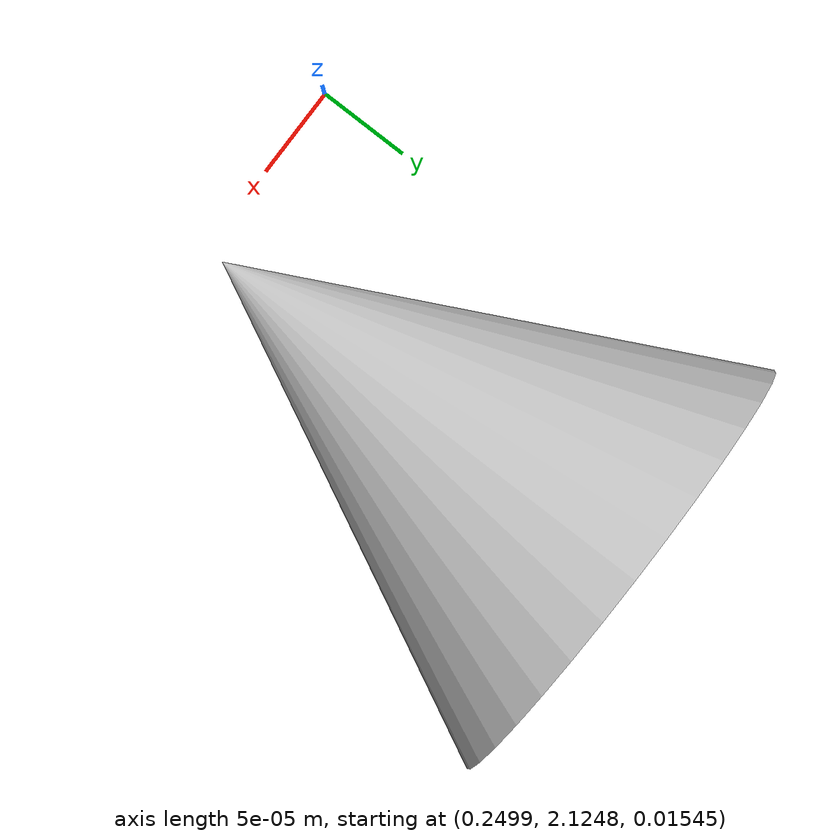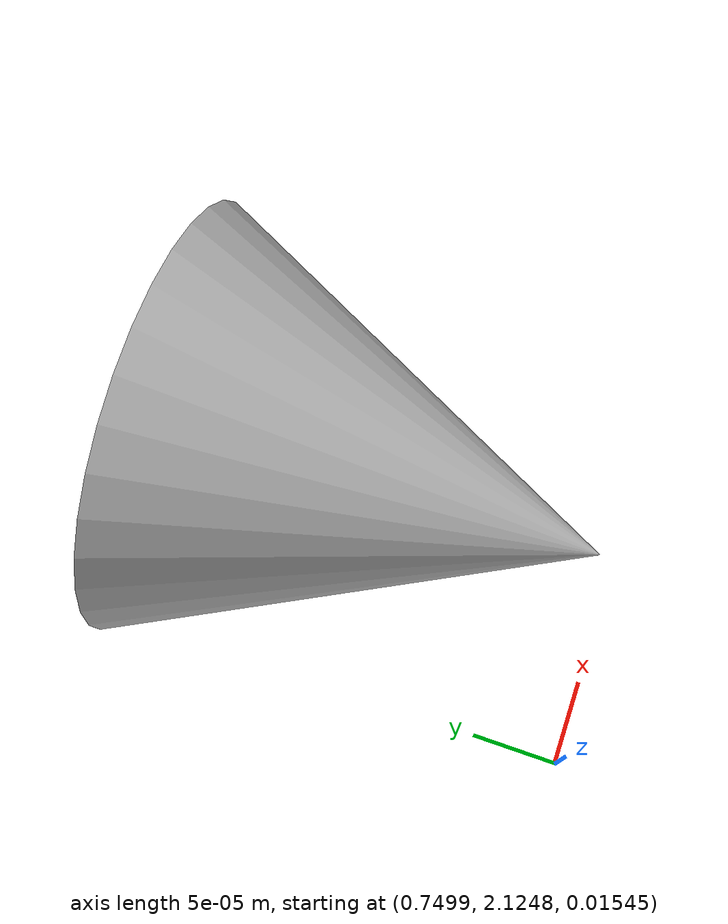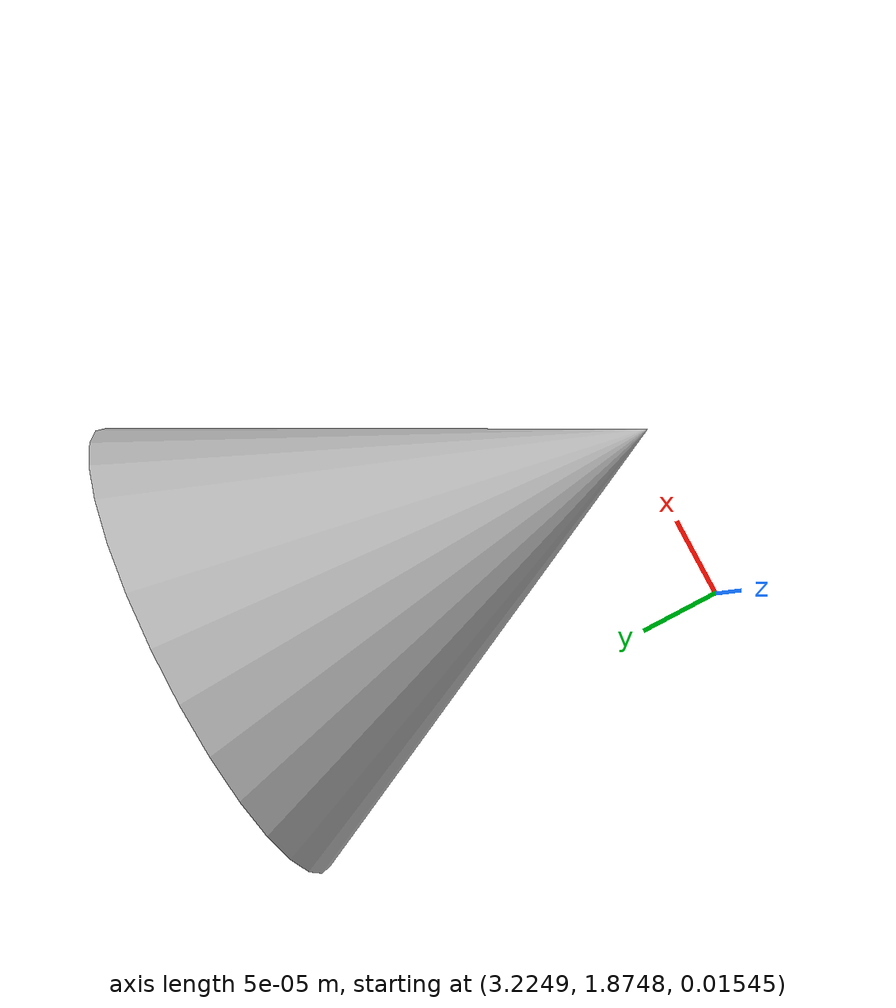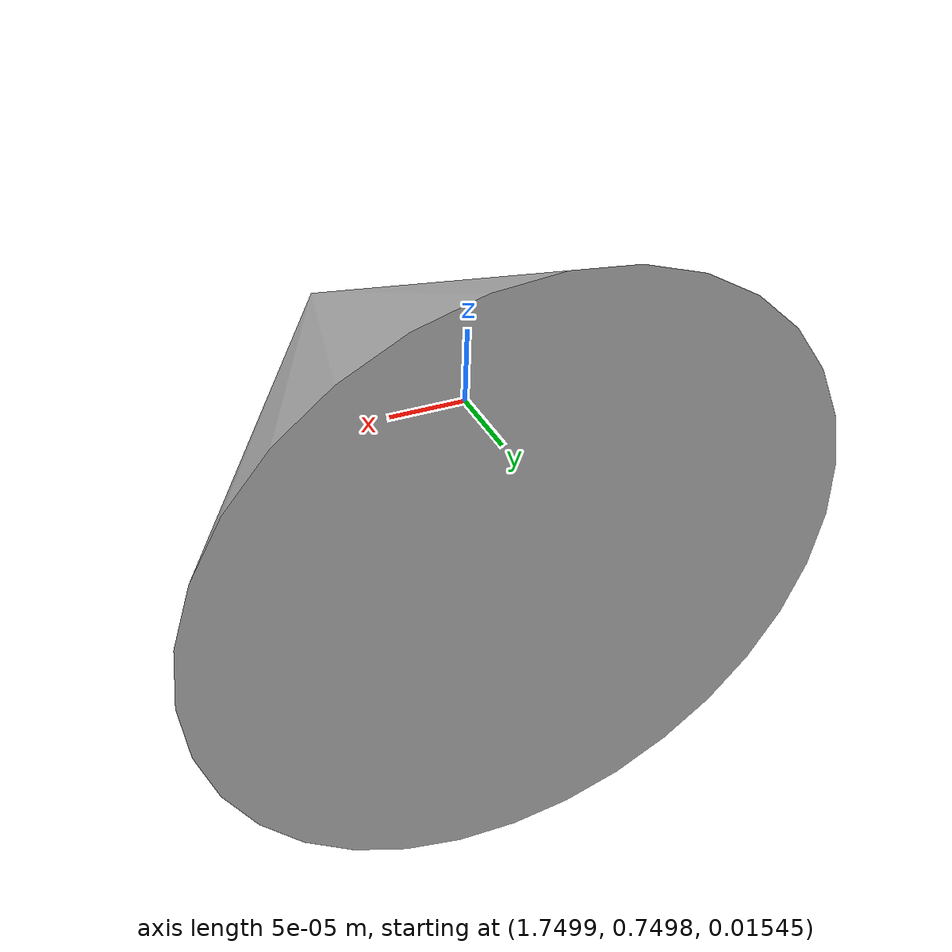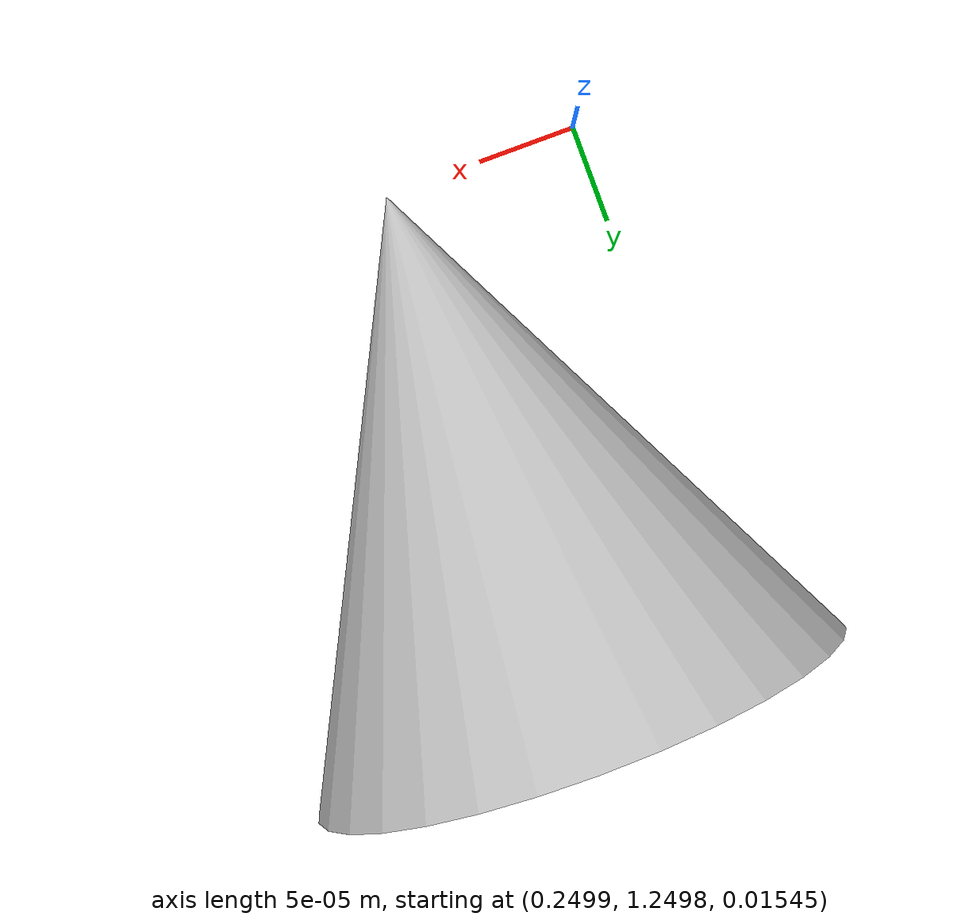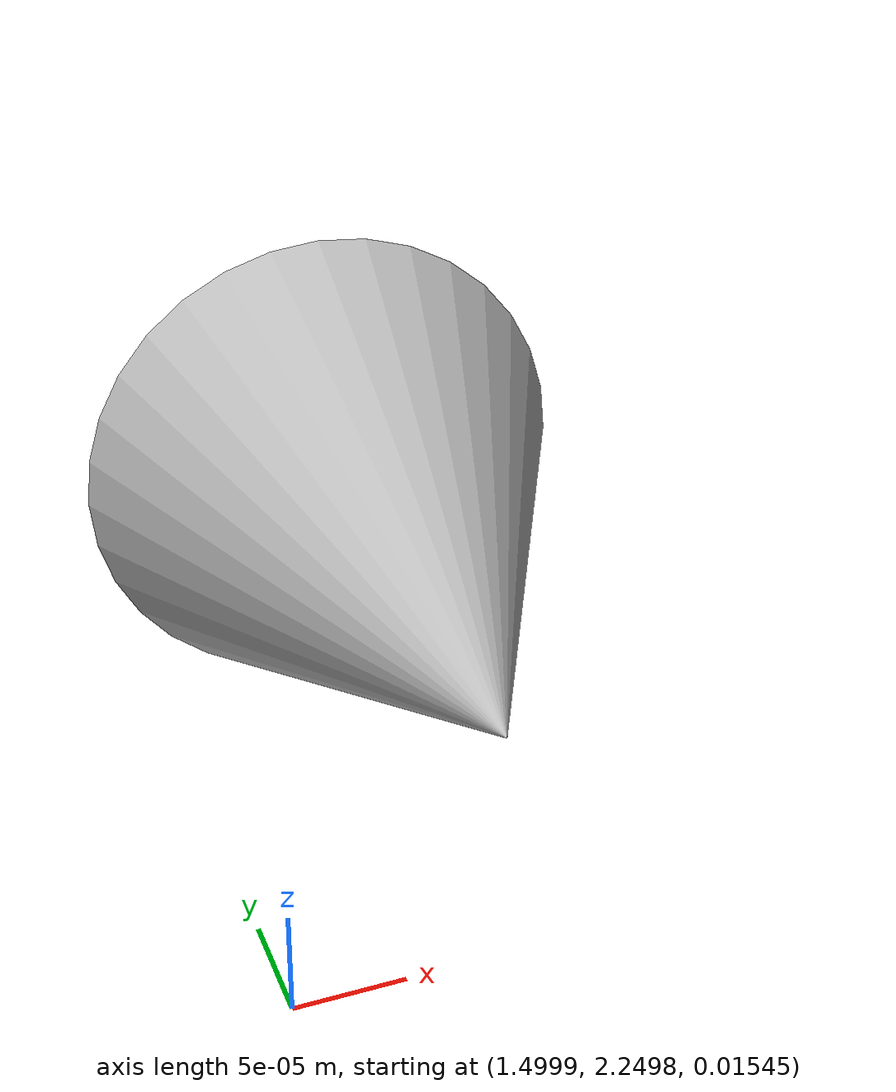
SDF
<sdf version="1.7">
 <world name="default">
  <gravity>0 0 -9.8</gravity>
  <magnetic_field>6e-06 2.3e-05 -4.2e-05</magnetic_field>
  <atmosphere type="adiabatic"/>
  <physics type="ode">
   <max_step_size>0.01</max_step_size>
   <real_time_factor>1</real_time_factor>
   <real_time_update_rate>100</real_time_update_rate>
  </physics>
  <scene>
   <ambient>1 1 1 1</ambient>
   <background>0.53 0.81 0.92 1</background>
   <shadows>0</shadows>
   <origin_visual>false</origin_visual>
  </scene>
  <spherical_coordinates>
   <surface_model>EARTH_WGS84</surface_model>
   <latitude_deg>0</latitude_deg>
   <longitude_deg>0</longitude_deg>
   <elevation>0</elevation>
   <heading_deg>0</heading_deg>
  </spherical_coordinates>
  <model name="person_standing">
   <link name="link">
    <inertial>
     <pose>2.9 0.47 0.01 0 -0  -1.09</pose>
     <mass>80</mass>
     <inertia>
      <ixx>24.879999999999999</ixx>
      <ixy>0</ixy>
      <ixz>0</ixz>
      <iyy>25.73</iyy>
      <iyz>0</iyz>
      <izz>2.48</izz>
     </inertia>
    </inertial>
    <collision name="bottom">
     <pose>0 -0.1 0.01 0 0 0</pose>
     <geometry><box><size>0.5 0.35 0.02</size></box></geometry>
    </collision>
    <collision name="person">
     <pose>0 0 0.02 0.04 0 0</pose>
     <geometry>
      <mesh><scale>0.2 0.2 0.2</scale><uri>model://person_standing/meshes/standing.dae</uri></mesh>
     </geometry>
    </collision>
    <visual name="visual">
     <pose>0 0 0.02 0.04 0 0</pose>
     <geometry>
      <mesh><scale>0.2 0.2 0.2</scale><uri>model://person_standing/meshes/standing.dae</uri></mesh>
     </geometry>
    </visual>
   </link>
   <pose>2.9 0.47 0.01 0 -0  -1.09</pose>
   <static>True</static>
  </model>
  <model name="model_obj_0_5_1_5">
   <static>True</static>
   <pose>0.25 0.75 0.015551519688861115 1.5707963267948966 -0  0.0</pose>
   <link name="link_obj_0_5_1_5">
    <collision name="collision_obj_0_5_1_5">
     <geometry><mesh><scale>0.0025 0.0025 0.0025</scale><uri>model://cone/meshes/cone.obj</uri></mesh></geometry>
    </collision>
    <visual name="visual_obj_0_5_1_5">
     <geometry>
      <mesh>
       <pose>0.25 0.75 0.015551519688861115 1.5707963267948966 -0  0.0</pose>
       <scale>0.0025 0.0025 0.0025</scale>
       <uri>model://cone/meshes/cone.obj</uri>
      </mesh>
     </geometry>
    </visual>
   </link>
  </model>
  <model name="model_obj_1_5_0_5">
   <static>True</static>
   <pose>0.75 0.25 0.015551519688861115 1.5707963267948966 -0  0.0</pose>
   <link name="link_obj_1_5_0_5">
    <collision name="collision_obj_1_5_0_5">
     <geometry><mesh><scale>0.0025 0.0025 0.0025</scale><uri>model://cone/meshes/cone.obj</uri></mesh></geometry>
    </collision>
    <visual name="visual_obj_1_5_0_5">
     <geometry>
      <mesh>
       <pose>0.75 0.25 0.015551519688861115 1.5707963267948966 -0  0.0</pose>
       <scale>0.0025 0.0025 0.0025</scale>
       <uri>model://cone/meshes/cone.obj</uri>
      </mesh>
     </geometry>
    </visual>
   </link>
  </model>
  <model name="model_obj_0_55_1_25">
   <static>True</static>
   <pose>0.275 0.625 0.015551519688861115 1.5707963267948966 -0  0.0</pose>
   <link name="link_obj_0_55_1_25">
    <collision name="collision_obj_0_55_1_25">
     <geometry><mesh><scale>0.0025 0.0025 0.0025</scale><uri>model://cone/meshes/cone.obj</uri></mesh></geometry>
    </collision>
    <visual name="visual_obj_0_55_1_25">
     <geometry>
      <mesh>
       <pose>0.275 0.625 0.015551519688861115 1.5707963267948966 -0  0.0</pose>
       <scale>0.0025 0.0025 0.0025</scale>
       <uri>model://cone/meshes/cone.obj</uri>
      </mesh>
     </geometry>
    </visual>
   </link>
  </model>
  <model name="model_obj_1_25_0_55">
   <static>True</static>
   <pose>0.625 0.275 0.015551519688861115 1.5707963267948966 -0  0.0</pose>
   <link name="link_obj_1_25_0_55">
    <collision name="collision_obj_1_25_0_55">
     <geometry><mesh><scale>0.0025 0.0025 0.0025</scale><uri>model://cone/meshes/cone.obj</uri></mesh></geometry>
    </collision>
    <visual name="visual_obj_1_25_0_55">
     <geometry>
      <mesh>
       <pose>0.625 0.275 0.015551519688861115 1.5707963267948966 -0  0.0</pose>
       <scale>0.0025 0.0025 0.0025</scale>
       <uri>model://cone/meshes/cone.obj</uri>
      </mesh>
     </geometry>
    </visual>
   </link>
  </model>
  <model name="model_obj_0_7_0_7">
   <static>True</static>
   <pose>0.35 0.35 0.015551519688861115 1.5707963267948966 -0  0.0</pose>
   <link name="link_obj_0_7_0_7">
    <collision name="collision_obj_0_7_0_7">
     <geometry><mesh><scale>0.0025 0.0025 0.0025</scale><uri>model://cone/meshes/cone.obj</uri></mesh></geometry>
    </collision>
    <visual name="visual_obj_0_7_0_7">
     <geometry>
      <mesh>
       <pose>0.35 0.35 0.015551519688861115 1.5707963267948966 -0  0.0</pose>
       <scale>0.0025 0.0025 0.0025</scale>
       <uri>model://cone/meshes/cone.obj</uri>
      </mesh>
     </geometry>
    </visual>
   </link>
  </model>
  <model name="model_obj_1_0_0_6000000000000001">
   <static>True</static>
   <pose>0.5 0.30000000000000004 0.015551519688861115 1.5707963267948966 -0  0.0</pose>
   <link name="link_obj_1_0_0_6000000000000001">
    <collision name="collision_obj_1_0_0_6000000000000001">
     <geometry><mesh><scale>0.0025 0.0025 0.0025</scale><uri>model://cone/meshes/cone.obj</uri></mesh></geometry>
    </collision>
    <visual name="visual_obj_1_0_0_6000000000000001">
     <geometry>
      <mesh>
       <pose>0.5 0.30000000000000004 0.015551519688861115 1.5707963267948966 -0  0.0</pose>
       <scale>0.0025 0.0025 0.0025</scale>
       <uri>model://cone/meshes/cone.obj</uri>
      </mesh>
     </geometry>
    </visual>
   </link>
  </model>
  <model name="model_obj_0_6000000000000001_1_0">
   <static>True</static>
   <pose>0.30000000000000004 0.5 0.015551519688861115 1.5707963267948966 -0  0.0</pose>
   <link name="link_obj_0_6000000000000001_1_0">
    <collision name="collision_obj_0_6000000000000001_1_0">
     <geometry><mesh><scale>0.0025 0.0025 0.0025</scale><uri>model://cone/meshes/cone.obj</uri></mesh></geometry>
    </collision>
    <visual name="visual_obj_0_6000000000000001_1_0">
     <geometry>
      <mesh>
       <pose>0.30000000000000004 0.5 0.015551519688861115 1.5707963267948966 -0  0.0</pose>
       <scale>0.0025 0.0025 0.0025</scale>
       <uri>model://cone/meshes/cone.obj</uri>
      </mesh>
     </geometry>
    </visual>
   </link>
  </model>
  <model name="model_obj_1_75_0_5">
   <static>True</static>
   <pose>0.875 0.25 0.015551519688861115 1.5707963267948966 -0  0.0</pose>
   <link name="link_obj_1_75_0_5">
    <collision name="collision_obj_1_75_0_5">
     <geometry><mesh><scale>0.0025 0.0025 0.0025</scale><uri>model://cone/meshes/cone.obj</uri></mesh></geometry>
    </collision>
    <visual name="visual_obj_1_75_0_5">
     <geometry>
      <mesh>
       <pose>0.875 0.25 0.015551519688861115 1.5707963267948966 -0  0.0</pose>
       <scale>0.0025 0.0025 0.0025</scale>
       <uri>model://cone/meshes/cone.obj</uri>
      </mesh>
     </geometry>
    </visual>
   </link>
  </model>
  <model name="model_obj_2_0_0_5">
   <static>True</static>
   <pose>1.0 0.25 0.015551519688861115 1.5707963267948966 -0  0.0</pose>
   <link name="link_obj_2_0_0_5">
    <collision name="collision_obj_2_0_0_5">
     <geometry><mesh><scale>0.0025 0.0025 0.0025</scale><uri>model://cone/meshes/cone.obj</uri></mesh></geometry>
    </collision>
    <visual name="visual_obj_2_0_0_5">
     <geometry>
      <mesh>
       <pose>1.0 0.25 0.015551519688861115 1.5707963267948966 -0  0.0</pose>
       <scale>0.0025 0.0025 0.0025</scale>
       <uri>model://cone/meshes/cone.obj</uri>
      </mesh>
     </geometry>
    </visual>
   </link>
  </model>
  <model name="model_obj_2_25_0_5">
   <static>True</static>
   <pose>1.125 0.25 0.015551519688861115 1.5707963267948966 -0  0.0</pose>
   <link name="link_obj_2_25_0_5">
    <collision name="collision_obj_2_25_0_5">
     <geometry><mesh><scale>0.0025 0.0025 0.0025</scale><uri>model://cone/meshes/cone.obj</uri></mesh></geometry>
    </collision>
    <visual name="visual_obj_2_25_0_5">
     <geometry>
      <mesh>
       <pose>1.125 0.25 0.015551519688861115 1.5707963267948966 -0  0.0</pose>
       <scale>0.0025 0.0025 0.0025</scale>
       <uri>model://cone/meshes/cone.obj</uri>
      </mesh>
     </geometry>
    </visual>
   </link>
  </model>
  <model name="model_obj_2_5_0_5">
   <static>True</static>
   <pose>1.25 0.25 0.015551519688861115 1.5707963267948966 -0  0.0</pose>
   <link name="link_obj_2_5_0_5">
    <collision name="collision_obj_2_5_0_5">
     <geometry><mesh><scale>0.0025 0.0025 0.0025</scale><uri>model://cone/meshes/cone.obj</uri></mesh></geometry>
    </collision>
    <visual name="visual_obj_2_5_0_5">
     <geometry>
      <mesh>
       <pose>1.25 0.25 0.015551519688861115 1.5707963267948966 -0  0.0</pose>
       <scale>0.0025 0.0025 0.0025</scale>
       <uri>model://cone/meshes/cone.obj</uri>
      </mesh>
     </geometry>
    </visual>
   </link>
  </model>
  <model name="model_obj_1_5_1_5">
   <static>True</static>
   <pose>0.75 0.75 0.015551519688861115 1.5707963267948966 -0  0.0</pose>
   <link name="link_obj_1_5_1_5">
    <collision name="collision_obj_1_5_1_5">
     <geometry><mesh><scale>0.0025 0.0025 0.0025</scale><uri>model://cone/meshes/cone.obj</uri></mesh></geometry>
    </collision>
    <visual name="visual_obj_1_5_1_5">
     <geometry>
      <mesh>
       <pose>0.75 0.75 0.015551519688861115 1.5707963267948966 -0  0.0</pose>
       <scale>0.0025 0.0025 0.0025</scale>
       <uri>model://cone/meshes/cone.obj</uri>
      </mesh>
     </geometry>
    </visual>
   </link>
  </model>
  <model name="model_obj_1_75_1_5">
   <static>True</static>
   <pose>0.875 0.75 0.015551519688861115 1.5707963267948966 -0  0.0</pose>
   <link name="link_obj_1_75_1_5">
    <collision name="collision_obj_1_75_1_5">
     <geometry><mesh><scale>0.0025 0.0025 0.0025</scale><uri>model://cone/meshes/cone.obj</uri></mesh></geometry>
    </collision>
    <visual name="visual_obj_1_75_1_5">
     <geometry>
      <mesh>
       <pose>0.875 0.75 0.015551519688861115 1.5707963267948966 -0  0.0</pose>
       <scale>0.0025 0.0025 0.0025</scale>
       <uri>model://cone/meshes/cone.obj</uri>
      </mesh>
     </geometry>
    </visual>
   </link>
  </model>
  <model name="model_obj_2_0_1_5">
   <static>True</static>
   <pose>1.0 0.75 0.015551519688861115 1.5707963267948966 -0  0.0</pose>
   <link name="link_obj_2_0_1_5">
    <collision name="collision_obj_2_0_1_5">
     <geometry><mesh><scale>0.0025 0.0025 0.0025</scale><uri>model://cone/meshes/cone.obj</uri></mesh></geometry>
    </collision>
    <visual name="visual_obj_2_0_1_5">
     <geometry>
      <mesh>
       <pose>1.0 0.75 0.015551519688861115 1.5707963267948966 -0  0.0</pose>
       <scale>0.0025 0.0025 0.0025</scale>
       <uri>model://cone/meshes/cone.obj</uri>
      </mesh>
     </geometry>
    </visual>
   </link>
  </model>
  <model name="model_obj_2_25_1_5">
   <static>True</static>
   <pose>1.125 0.75 0.015551519688861115 1.5707963267948966 -0  0.0</pose>
   <link name="link_obj_2_25_1_5">
    <collision name="collision_obj_2_25_1_5">
     <geometry><mesh><scale>0.0025 0.0025 0.0025</scale><uri>model://cone/meshes/cone.obj</uri></mesh></geometry>
    </collision>
    <visual name="visual_obj_2_25_1_5">
     <geometry>
      <mesh>
       <pose>1.125 0.75 0.015551519688861115 1.5707963267948966 -0  0.0</pose>
       <scale>0.0025 0.0025 0.0025</scale>
       <uri>model://cone/meshes/cone.obj</uri>
      </mesh>
     </geometry>
    </visual>
   </link>
  </model>
  <model name="model_obj_2_5_1_5">
   <static>True</static>
   <pose>1.25 0.75 0.015551519688861115 1.5707963267948966 -0  0.0</pose>
   <link name="link_obj_2_5_1_5">
    <collision name="collision_obj_2_5_1_5">
     <geometry><mesh><scale>0.0025 0.0025 0.0025</scale><uri>model://cone/meshes/cone.obj</uri></mesh></geometry>
    </collision>
    <visual name="visual_obj_2_5_1_5">
     <geometry>
      <mesh>
       <pose>1.25 0.75 0.015551519688861115 1.5707963267948966 -0  0.0</pose>
       <scale>0.0025 0.0025 0.0025</scale>
       <uri>model://cone/meshes/cone.obj</uri>
      </mesh>
     </geometry>
    </visual>
   </link>
  </model>
  <model name="model_obj_2_75_0_5">
   <static>True</static>
   <pose>1.375 0.25 0.015551519688861115 1.5707963267948966 -0  0.0</pose>
   <link name="link_obj_2_75_0_5">
    <collision name="collision_obj_2_75_0_5">
     <geometry><mesh><scale>0.0025 0.0025 0.0025</scale><uri>model://cone/meshes/cone.obj</uri></mesh></geometry>
    </collision>
    <visual name="visual_obj_2_75_0_5">
     <geometry>
      <mesh>
       <pose>1.375 0.25 0.015551519688861115 1.5707963267948966 -0  0.0</pose>
       <scale>0.0025 0.0025 0.0025</scale>
       <uri>model://cone/meshes/cone.obj</uri>
      </mesh>
     </geometry>
    </visual>
   </link>
  </model>
  <model name="model_obj_3_0_0_5">
   <static>True</static>
   <pose>1.5 0.25 0.015551519688861115 1.5707963267948966 -0  0.0</pose>
   <link name="link_obj_3_0_0_5">
    <collision name="collision_obj_3_0_0_5">
     <geometry><mesh><scale>0.0025 0.0025 0.0025</scale><uri>model://cone/meshes/cone.obj</uri></mesh></geometry>
    </collision>
    <visual name="visual_obj_3_0_0_5">
     <geometry>
      <mesh>
       <pose>1.5 0.25 0.015551519688861115 1.5707963267948966 -0  0.0</pose>
       <scale>0.0025 0.0025 0.0025</scale>
       <uri>model://cone/meshes/cone.obj</uri>
      </mesh>
     </geometry>
    </visual>
   </link>
  </model>
  <model name="model_obj_3_25_0_5">
   <static>True</static>
   <pose>1.625 0.25 0.015551519688861115 1.5707963267948966 -0  0.0</pose>
   <link name="link_obj_3_25_0_5">
    <collision name="collision_obj_3_25_0_5">
     <geometry><mesh><scale>0.0025 0.0025 0.0025</scale><uri>model://cone/meshes/cone.obj</uri></mesh></geometry>
    </collision>
    <visual name="visual_obj_3_25_0_5">
     <geometry>
      <mesh>
       <pose>1.625 0.25 0.015551519688861115 1.5707963267948966 -0  0.0</pose>
       <scale>0.0025 0.0025 0.0025</scale>
       <uri>model://cone/meshes/cone.obj</uri>
      </mesh>
     </geometry>
    </visual>
   </link>
  </model>
  <model name="model_obj_3_5_0_5">
   <static>True</static>
   <pose>1.75 0.25 0.015551519688861115 1.5707963267948966 -0  0.0</pose>
   <link name="link_obj_3_5_0_5">
    <collision name="collision_obj_3_5_0_5">
     <geometry><mesh><scale>0.0025 0.0025 0.0025</scale><uri>model://cone/meshes/cone.obj</uri></mesh></geometry>
    </collision>
    <visual name="visual_obj_3_5_0_5">
     <geometry>
      <mesh>
       <pose>1.75 0.25 0.015551519688861115 1.5707963267948966 -0  0.0</pose>
       <scale>0.0025 0.0025 0.0025</scale>
       <uri>model://cone/meshes/cone.obj</uri>
      </mesh>
     </geometry>
    </visual>
   </link>
  </model>
  <model name="model_obj_2_75_1_5">
   <static>True</static>
   <pose>1.375 0.75 0.015551519688861115 1.5707963267948966 -0  0.0</pose>
   <link name="link_obj_2_75_1_5">
    <collision name="collision_obj_2_75_1_5">
     <geometry><mesh><scale>0.0025 0.0025 0.0025</scale><uri>model://cone/meshes/cone.obj</uri></mesh></geometry>
    </collision>
    <visual name="visual_obj_2_75_1_5">
     <geometry>
      <mesh>
       <pose>1.375 0.75 0.015551519688861115 1.5707963267948966 -0  0.0</pose>
       <scale>0.0025 0.0025 0.0025</scale>
       <uri>model://cone/meshes/cone.obj</uri>
      </mesh>
     </geometry>
    </visual>
   </link>
  </model>
  <model name="model_obj_3_0_1_5">
   <static>True</static>
   <pose>1.5 0.75 0.015551519688861115 1.5707963267948966 -0  0.0</pose>
   <link name="link_obj_3_0_1_5">
    <collision name="collision_obj_3_0_1_5">
     <geometry><mesh><scale>0.0025 0.0025 0.0025</scale><uri>model://cone/meshes/cone.obj</uri></mesh></geometry>
    </collision>
    <visual name="visual_obj_3_0_1_5">
     <geometry>
      <mesh>
       <pose>1.5 0.75 0.015551519688861115 1.5707963267948966 -0  0.0</pose>
       <scale>0.0025 0.0025 0.0025</scale>
       <uri>model://cone/meshes/cone.obj</uri>
      </mesh>
     </geometry>
    </visual>
   </link>
  </model>
  <model name="model_obj_3_25_1_5">
   <static>True</static>
   <pose>1.625 0.75 0.015551519688861115 1.5707963267948966 -0  0.0</pose>
   <link name="link_obj_3_25_1_5">
    <collision name="collision_obj_3_25_1_5">
     <geometry><mesh><scale>0.0025 0.0025 0.0025</scale><uri>model://cone/meshes/cone.obj</uri></mesh></geometry>
    </collision>
    <visual name="visual_obj_3_25_1_5">
     <geometry>
      <mesh>
       <pose>1.625 0.75 0.015551519688861115 1.5707963267948966 -0  0.0</pose>
       <scale>0.0025 0.0025 0.0025</scale>
       <uri>model://cone/meshes/cone.obj</uri>
      </mesh>
     </geometry>
    </visual>
   </link>
  </model>
  <model name="model_obj_3_5_1_5">
   <static>True</static>
   <pose>1.75 0.75 0.015551519688861115 1.5707963267948966 -0  0.0</pose>
   <link name="link_obj_3_5_1_5">
    <collision name="collision_obj_3_5_1_5">
     <geometry><mesh><scale>0.0025 0.0025 0.0025</scale><uri>model://cone/meshes/cone.obj</uri></mesh></geometry>
    </collision>
    <visual name="visual_obj_3_5_1_5">
     <geometry>
      <mesh>
       <pose>1.75 0.75 0.015551519688861115 1.5707963267948966 -0  0.0</pose>
       <scale>0.0025 0.0025 0.0025</scale>
       <uri>model://cone/meshes/cone.obj</uri>
      </mesh>
     </geometry>
    </visual>
   </link>
  </model>
  <model name="model_obj_3_75_0_5">
   <static>True</static>
   <pose>1.875 0.25 0.015551519688861115 1.5707963267948966 -0  0.0</pose>
   <link name="link_obj_3_75_0_5">
    <collision name="collision_obj_3_75_0_5">
     <geometry><mesh><scale>0.0025 0.0025 0.0025</scale><uri>model://cone/meshes/cone.obj</uri></mesh></geometry>
    </collision>
    <visual name="visual_obj_3_75_0_5">
     <geometry>
      <mesh>
       <pose>1.875 0.25 0.015551519688861115 1.5707963267948966 -0  0.0</pose>
       <scale>0.0025 0.0025 0.0025</scale>
       <uri>model://cone/meshes/cone.obj</uri>
      </mesh>
     </geometry>
    </visual>
   </link>
  </model>
  <model name="model_obj_4_0_0_5">
   <static>True</static>
   <pose>2.0 0.25 0.015551519688861115 1.5707963267948966 -0  0.0</pose>
   <link name="link_obj_4_0_0_5">
    <collision name="collision_obj_4_0_0_5">
     <geometry><mesh><scale>0.0025 0.0025 0.0025</scale><uri>model://cone/meshes/cone.obj</uri></mesh></geometry>
    </collision>
    <visual name="visual_obj_4_0_0_5">
     <geometry>
      <mesh>
       <pose>2.0 0.25 0.015551519688861115 1.5707963267948966 -0  0.0</pose>
       <scale>0.0025 0.0025 0.0025</scale>
       <uri>model://cone/meshes/cone.obj</uri>
      </mesh>
     </geometry>
    </visual>
   </link>
  </model>
  <model name="model_obj_4_25_0_5">
   <static>True</static>
   <pose>2.125 0.25 0.015551519688861115 1.5707963267948966 -0  0.0</pose>
   <link name="link_obj_4_25_0_5">
    <collision name="collision_obj_4_25_0_5">
     <geometry><mesh><scale>0.0025 0.0025 0.0025</scale><uri>model://cone/meshes/cone.obj</uri></mesh></geometry>
    </collision>
    <visual name="visual_obj_4_25_0_5">
     <geometry>
      <mesh>
       <pose>2.125 0.25 0.015551519688861115 1.5707963267948966 -0  0.0</pose>
       <scale>0.0025 0.0025 0.0025</scale>
       <uri>model://cone/meshes/cone.obj</uri>
      </mesh>
     </geometry>
    </visual>
   </link>
  </model>
  <model name="model_obj_4_5_0_5">
   <static>True</static>
   <pose>2.25 0.25 0.015551519688861115 1.5707963267948966 -0  0.0</pose>
   <link name="link_obj_4_5_0_5">
    <collision name="collision_obj_4_5_0_5">
     <geometry><mesh><scale>0.0025 0.0025 0.0025</scale><uri>model://cone/meshes/cone.obj</uri></mesh></geometry>
    </collision>
    <visual name="visual_obj_4_5_0_5">
     <geometry>
      <mesh>
       <pose>2.25 0.25 0.015551519688861115 1.5707963267948966 -0  0.0</pose>
       <scale>0.0025 0.0025 0.0025</scale>
       <uri>model://cone/meshes/cone.obj</uri>
      </mesh>
     </geometry>
    </visual>
   </link>
  </model>
  <model name="model_obj_3_75_1_5">
   <static>True</static>
   <pose>1.875 0.75 0.015551519688861115 1.5707963267948966 -0  0.0</pose>
   <link name="link_obj_3_75_1_5">
    <collision name="collision_obj_3_75_1_5">
     <geometry><mesh><scale>0.0025 0.0025 0.0025</scale><uri>model://cone/meshes/cone.obj</uri></mesh></geometry>
    </collision>
    <visual name="visual_obj_3_75_1_5">
     <geometry>
      <mesh>
       <pose>1.875 0.75 0.015551519688861115 1.5707963267948966 -0  0.0</pose>
       <scale>0.0025 0.0025 0.0025</scale>
       <uri>model://cone/meshes/cone.obj</uri>
      </mesh>
     </geometry>
    </visual>
   </link>
  </model>
  <model name="model_obj_4_0_1_5">
   <static>True</static>
   <pose>2.0 0.75 0.015551519688861115 1.5707963267948966 -0  0.0</pose>
   <link name="link_obj_4_0_1_5">
    <collision name="collision_obj_4_0_1_5">
     <geometry><mesh><scale>0.0025 0.0025 0.0025</scale><uri>model://cone/meshes/cone.obj</uri></mesh></geometry>
    </collision>
    <visual name="visual_obj_4_0_1_5">
     <geometry>
      <mesh>
       <pose>2.0 0.75 0.015551519688861115 1.5707963267948966 -0  0.0</pose>
       <scale>0.0025 0.0025 0.0025</scale>
       <uri>model://cone/meshes/cone.obj</uri>
      </mesh>
     </geometry>
    </visual>
   </link>
  </model>
  <model name="model_obj_4_25_1_5">
   <static>True</static>
   <pose>2.125 0.75 0.015551519688861115 1.5707963267948966 -0  0.0</pose>
   <link name="link_obj_4_25_1_5">
    <collision name="collision_obj_4_25_1_5">
     <geometry><mesh><scale>0.0025 0.0025 0.0025</scale><uri>model://cone/meshes/cone.obj</uri></mesh></geometry>
    </collision>
    <visual name="visual_obj_4_25_1_5">
     <geometry>
      <mesh>
       <pose>2.125 0.75 0.015551519688861115 1.5707963267948966 -0  0.0</pose>
       <scale>0.0025 0.0025 0.0025</scale>
       <uri>model://cone/meshes/cone.obj</uri>
      </mesh>
     </geometry>
    </visual>
   </link>
  </model>
  <model name="model_obj_4_5_1_5">
   <static>True</static>
   <pose>2.25 0.75 0.015551519688861115 1.5707963267948966 -0  0.0</pose>
   <link name="link_obj_4_5_1_5">
    <collision name="collision_obj_4_5_1_5">
     <geometry><mesh><scale>0.0025 0.0025 0.0025</scale><uri>model://cone/meshes/cone.obj</uri></mesh></geometry>
    </collision>
    <visual name="visual_obj_4_5_1_5">
     <geometry>
      <mesh>
       <pose>2.25 0.75 0.015551519688861115 1.5707963267948966 -0  0.0</pose>
       <scale>0.0025 0.0025 0.0025</scale>
       <uri>model://cone/meshes/cone.obj</uri>
      </mesh>
     </geometry>
    </visual>
   </link>
  </model>
  <model name="model_obj_4_75_0_5">
   <static>True</static>
   <pose>2.375 0.25 0.015551519688861115 1.5707963267948966 -0  0.0</pose>
   <link name="link_obj_4_75_0_5">
    <collision name="collision_obj_4_75_0_5">
     <geometry><mesh><scale>0.0025 0.0025 0.0025</scale><uri>model://cone/meshes/cone.obj</uri></mesh></geometry>
    </collision>
    <visual name="visual_obj_4_75_0_5">
     <geometry>
      <mesh>
       <pose>2.375 0.25 0.015551519688861115 1.5707963267948966 -0  0.0</pose>
       <scale>0.0025 0.0025 0.0025</scale>
       <uri>model://cone/meshes/cone.obj</uri>
      </mesh>
     </geometry>
    </visual>
   </link>
  </model>
  <model name="model_obj_5_0_0_5">
   <static>True</static>
   <pose>2.5 0.25 0.015551519688861115 1.5707963267948966 -0  0.0</pose>
   <link name="link_obj_5_0_0_5">
    <collision name="collision_obj_5_0_0_5">
     <geometry><mesh><scale>0.0025 0.0025 0.0025</scale><uri>model://cone/meshes/cone.obj</uri></mesh></geometry>
    </collision>
    <visual name="visual_obj_5_0_0_5">
     <geometry>
      <mesh>
       <pose>2.5 0.25 0.015551519688861115 1.5707963267948966 -0  0.0</pose>
       <scale>0.0025 0.0025 0.0025</scale>
       <uri>model://cone/meshes/cone.obj</uri>
      </mesh>
     </geometry>
    </visual>
   </link>
  </model>
  <model name="model_obj_5_25_0_5">
   <static>True</static>
   <pose>2.625 0.25 0.015551519688861115 1.5707963267948966 -0  0.0</pose>
   <link name="link_obj_5_25_0_5">
    <collision name="collision_obj_5_25_0_5">
     <geometry><mesh><scale>0.0025 0.0025 0.0025</scale><uri>model://cone/meshes/cone.obj</uri></mesh></geometry>
    </collision>
    <visual name="visual_obj_5_25_0_5">
     <geometry>
      <mesh>
       <pose>2.625 0.25 0.015551519688861115 1.5707963267948966 -0  0.0</pose>
       <scale>0.0025 0.0025 0.0025</scale>
       <uri>model://cone/meshes/cone.obj</uri>
      </mesh>
     </geometry>
    </visual>
   </link>
  </model>
  <model name="model_obj_5_5_0_5">
   <static>True</static>
   <pose>2.75 0.25 0.015551519688861115 1.5707963267948966 -0  0.0</pose>
   <link name="link_obj_5_5_0_5">
    <collision name="collision_obj_5_5_0_5">
     <geometry><mesh><scale>0.0025 0.0025 0.0025</scale><uri>model://cone/meshes/cone.obj</uri></mesh></geometry>
    </collision>
    <visual name="visual_obj_5_5_0_5">
     <geometry>
      <mesh>
       <pose>2.75 0.25 0.015551519688861115 1.5707963267948966 -0  0.0</pose>
       <scale>0.0025 0.0025 0.0025</scale>
       <uri>model://cone/meshes/cone.obj</uri>
      </mesh>
     </geometry>
    </visual>
   </link>
  </model>
  <model name="model_obj_4_75_1_5">
   <static>True</static>
   <pose>2.375 0.75 0.015551519688861115 1.5707963267948966 -0  0.0</pose>
   <link name="link_obj_4_75_1_5">
    <collision name="collision_obj_4_75_1_5">
     <geometry><mesh><scale>0.0025 0.0025 0.0025</scale><uri>model://cone/meshes/cone.obj</uri></mesh></geometry>
    </collision>
    <visual name="visual_obj_4_75_1_5">
     <geometry>
      <mesh>
       <pose>2.375 0.75 0.015551519688861115 1.5707963267948966 -0  0.0</pose>
       <scale>0.0025 0.0025 0.0025</scale>
       <uri>model://cone/meshes/cone.obj</uri>
      </mesh>
     </geometry>
    </visual>
   </link>
  </model>
  <model name="model_obj_5_0_1_5">
   <static>True</static>
   <pose>2.5 0.75 0.015551519688861115 1.5707963267948966 -0  0.0</pose>
   <link name="link_obj_5_0_1_5">
    <collision name="collision_obj_5_0_1_5">
     <geometry><mesh><scale>0.0025 0.0025 0.0025</scale><uri>model://cone/meshes/cone.obj</uri></mesh></geometry>
    </collision>
    <visual name="visual_obj_5_0_1_5">
     <geometry>
      <mesh>
       <pose>2.5 0.75 0.015551519688861115 1.5707963267948966 -0  0.0</pose>
       <scale>0.0025 0.0025 0.0025</scale>
       <uri>model://cone/meshes/cone.obj</uri>
      </mesh>
     </geometry>
    </visual>
   </link>
  </model>
  <model name="model_obj_5_25_1_5">
   <static>True</static>
   <pose>2.625 0.75 0.015551519688861115 1.5707963267948966 -0  0.0</pose>
   <link name="link_obj_5_25_1_5">
    <collision name="collision_obj_5_25_1_5">
     <geometry><mesh><scale>0.0025 0.0025 0.0025</scale><uri>model://cone/meshes/cone.obj</uri></mesh></geometry>
    </collision>
    <visual name="visual_obj_5_25_1_5">
     <geometry>
      <mesh>
       <pose>2.625 0.75 0.015551519688861115 1.5707963267948966 -0  0.0</pose>
       <scale>0.0025 0.0025 0.0025</scale>
       <uri>model://cone/meshes/cone.obj</uri>
      </mesh>
     </geometry>
    </visual>
   </link>
  </model>
  <model name="model_obj_5_5_1_5">
   <static>True</static>
   <pose>2.75 0.75 0.015551519688861115 1.5707963267948966 -0  0.0</pose>
   <link name="link_obj_5_5_1_5">
    <collision name="collision_obj_5_5_1_5">
     <geometry><mesh><scale>0.0025 0.0025 0.0025</scale><uri>model://cone/meshes/cone.obj</uri></mesh></geometry>
    </collision>
    <visual name="visual_obj_5_5_1_5">
     <geometry>
      <mesh>
       <pose>2.75 0.75 0.015551519688861115 1.5707963267948966 -0  0.0</pose>
       <scale>0.0025 0.0025 0.0025</scale>
       <uri>model://cone/meshes/cone.obj</uri>
      </mesh>
     </geometry>
    </visual>
   </link>
  </model>
  <model name="model_obj_6_5_1_5">
   <static>True</static>
   <pose>3.25 0.75 0.015551519688861115 1.5707963267948966 -0  0.0</pose>
   <link name="link_obj_6_5_1_5">
    <collision name="collision_obj_6_5_1_5">
     <geometry><mesh><scale>0.0025 0.0025 0.0025</scale><uri>model://cone/meshes/cone.obj</uri></mesh></geometry>
    </collision>
    <visual name="visual_obj_6_5_1_5">
     <geometry>
      <mesh>
       <pose>3.25 0.75 0.015551519688861115 1.5707963267948966 -0  0.0</pose>
       <scale>0.0025 0.0025 0.0025</scale>
       <uri>model://cone/meshes/cone.obj</uri>
      </mesh>
     </geometry>
    </visual>
   </link>
  </model>
  <model name="model_obj_5_75_0_55">
   <static>True</static>
   <pose>2.875 0.275 0.015551519688861115 1.5707963267948966 -0  0.0</pose>
   <link name="link_obj_5_75_0_55">
    <collision name="collision_obj_5_75_0_55">
     <geometry><mesh><scale>0.0025 0.0025 0.0025</scale><uri>model://cone/meshes/cone.obj</uri></mesh></geometry>
    </collision>
    <visual name="visual_obj_5_75_0_55">
     <geometry>
      <mesh>
       <pose>2.875 0.275 0.015551519688861115 1.5707963267948966 -0  0.0</pose>
       <scale>0.0025 0.0025 0.0025</scale>
       <uri>model://cone/meshes/cone.obj</uri>
      </mesh>
     </geometry>
    </visual>
   </link>
  </model>
  <model name="model_obj_6_45_1_25">
   <static>True</static>
   <pose>3.225 0.625 0.015551519688861115 1.5707963267948966 -0  0.0</pose>
   <link name="link_obj_6_45_1_25">
    <collision name="collision_obj_6_45_1_25">
     <geometry><mesh><scale>0.0025 0.0025 0.0025</scale><uri>model://cone/meshes/cone.obj</uri></mesh></geometry>
    </collision>
    <visual name="visual_obj_6_45_1_25">
     <geometry>
      <mesh>
       <pose>3.225 0.625 0.015551519688861115 1.5707963267948966 -0  0.0</pose>
       <scale>0.0025 0.0025 0.0025</scale>
       <uri>model://cone/meshes/cone.obj</uri>
      </mesh>
     </geometry>
    </visual>
   </link>
  </model>
  <model name="model_obj_6_3_0_7">
   <static>True</static>
   <pose>3.15 0.35 0.015551519688861115 1.5707963267948966 -0  0.0</pose>
   <link name="link_obj_6_3_0_7">
    <collision name="collision_obj_6_3_0_7">
     <geometry><mesh><scale>0.0025 0.0025 0.0025</scale><uri>model://cone/meshes/cone.obj</uri></mesh></geometry>
    </collision>
    <visual name="visual_obj_6_3_0_7">
     <geometry>
      <mesh>
       <pose>3.15 0.35 0.015551519688861115 1.5707963267948966 -0  0.0</pose>
       <scale>0.0025 0.0025 0.0025</scale>
       <uri>model://cone/meshes/cone.obj</uri>
      </mesh>
     </geometry>
    </visual>
   </link>
  </model>
  <model name="model_obj_6_4_1_0">
   <static>True</static>
   <pose>3.2 0.5 0.015551519688861115 1.5707963267948966 -0  0.0</pose>
   <link name="link_obj_6_4_1_0">
    <collision name="collision_obj_6_4_1_0">
     <geometry><mesh><scale>0.0025 0.0025 0.0025</scale><uri>model://cone/meshes/cone.obj</uri></mesh></geometry>
    </collision>
    <visual name="visual_obj_6_4_1_0">
     <geometry>
      <mesh>
       <pose>3.2 0.5 0.015551519688861115 1.5707963267948966 -0  0.0</pose>
       <scale>0.0025 0.0025 0.0025</scale>
       <uri>model://cone/meshes/cone.obj</uri>
      </mesh>
     </geometry>
    </visual>
   </link>
  </model>
  <model name="model_obj_6_0_0_6000000000000001">
   <static>True</static>
   <pose>3.0 0.30000000000000004 0.015551519688861115 1.5707963267948966 -0  0.0</pose>
   <link name="link_obj_6_0_0_6000000000000001">
    <collision name="collision_obj_6_0_0_6000000000000001">
     <geometry><mesh><scale>0.0025 0.0025 0.0025</scale><uri>model://cone/meshes/cone.obj</uri></mesh></geometry>
    </collision>
    <visual name="visual_obj_6_0_0_6000000000000001">
     <geometry>
      <mesh>
       <pose>3.0 0.30000000000000004 0.015551519688861115 1.5707963267948966 -0  0.0</pose>
       <scale>0.0025 0.0025 0.0025</scale>
       <uri>model://cone/meshes/cone.obj</uri>
      </mesh>
     </geometry>
    </visual>
   </link>
  </model>
  <model name="model_obj_0_5_1_75">
   <static>True</static>
   <pose>0.25 0.875 0.015551519688861115 1.5707963267948966 -0  0.0</pose>
   <link name="link_obj_0_5_1_75">
    <collision name="collision_obj_0_5_1_75">
     <geometry><mesh><scale>0.0025 0.0025 0.0025</scale><uri>model://cone/meshes/cone.obj</uri></mesh></geometry>
    </collision>
    <visual name="visual_obj_0_5_1_75">
     <geometry>
      <mesh>
       <pose>0.25 0.875 0.015551519688861115 1.5707963267948966 -0  0.0</pose>
       <scale>0.0025 0.0025 0.0025</scale>
       <uri>model://cone/meshes/cone.obj</uri>
      </mesh>
     </geometry>
    </visual>
   </link>
  </model>
  <model name="model_obj_0_5_2_0">
   <static>True</static>
   <pose>0.25 1.0 0.015551519688861115 1.5707963267948966 -0  0.0</pose>
   <link name="link_obj_0_5_2_0">
    <collision name="collision_obj_0_5_2_0">
     <geometry><mesh><scale>0.0025 0.0025 0.0025</scale><uri>model://cone/meshes/cone.obj</uri></mesh></geometry>
    </collision>
    <visual name="visual_obj_0_5_2_0">
     <geometry>
      <mesh>
       <pose>0.25 1.0 0.015551519688861115 1.5707963267948966 -0  0.0</pose>
       <scale>0.0025 0.0025 0.0025</scale>
       <uri>model://cone/meshes/cone.obj</uri>
      </mesh>
     </geometry>
    </visual>
   </link>
  </model>
  <model name="model_obj_0_5_2_25">
   <static>True</static>
   <pose>0.25 1.125 0.015551519688861115 1.5707963267948966 -0  0.0</pose>
   <link name="link_obj_0_5_2_25">
    <collision name="collision_obj_0_5_2_25">
     <geometry><mesh><scale>0.0025 0.0025 0.0025</scale><uri>model://cone/meshes/cone.obj</uri></mesh></geometry>
    </collision>
    <visual name="visual_obj_0_5_2_25">
     <geometry>
      <mesh>
       <pose>0.25 1.125 0.015551519688861115 1.5707963267948966 -0  0.0</pose>
       <scale>0.0025 0.0025 0.0025</scale>
       <uri>model://cone/meshes/cone.obj</uri>
      </mesh>
     </geometry>
    </visual>
   </link>
  </model>
  <model name="model_obj_0_5_2_5">
   <static>True</static>
   <pose>0.25 1.25 0.015551519688861115 1.5707963267948966 -0  0.0</pose>
   <link name="link_obj_0_5_2_5">
    <collision name="collision_obj_0_5_2_5">
     <geometry><mesh><scale>0.0025 0.0025 0.0025</scale><uri>model://cone/meshes/cone.obj</uri></mesh></geometry>
    </collision>
    <visual name="visual_obj_0_5_2_5">
     <geometry>
      <mesh>
       <pose>0.25 1.25 0.015551519688861115 1.5707963267948966 -0  0.0</pose>
       <scale>0.0025 0.0025 0.0025</scale>
       <uri>model://cone/meshes/cone.obj</uri>
      </mesh>
     </geometry>
    </visual>
   </link>
  </model>
  <model name="model_obj_1_5_1_75">
   <static>True</static>
   <pose>0.75 0.875 0.015551519688861115 1.5707963267948966 -0  0.0</pose>
   <link name="link_obj_1_5_1_75">
    <collision name="collision_obj_1_5_1_75">
     <geometry><mesh><scale>0.0025 0.0025 0.0025</scale><uri>model://cone/meshes/cone.obj</uri></mesh></geometry>
    </collision>
    <visual name="visual_obj_1_5_1_75">
     <geometry>
      <mesh>
       <pose>0.75 0.875 0.015551519688861115 1.5707963267948966 -0  0.0</pose>
       <scale>0.0025 0.0025 0.0025</scale>
       <uri>model://cone/meshes/cone.obj</uri>
      </mesh>
     </geometry>
    </visual>
   </link>
  </model>
  <model name="model_obj_1_5_2_0">
   <static>True</static>
   <pose>0.75 1.0 0.015551519688861115 1.5707963267948966 -0  0.0</pose>
   <link name="link_obj_1_5_2_0">
    <collision name="collision_obj_1_5_2_0">
     <geometry><mesh><scale>0.0025 0.0025 0.0025</scale><uri>model://cone/meshes/cone.obj</uri></mesh></geometry>
    </collision>
    <visual name="visual_obj_1_5_2_0">
     <geometry>
      <mesh>
       <pose>0.75 1.0 0.015551519688861115 1.5707963267948966 -0  0.0</pose>
       <scale>0.0025 0.0025 0.0025</scale>
       <uri>model://cone/meshes/cone.obj</uri>
      </mesh>
     </geometry>
    </visual>
   </link>
  </model>
  <model name="model_obj_1_5_2_25">
   <static>True</static>
   <pose>0.75 1.125 0.015551519688861115 1.5707963267948966 -0  0.0</pose>
   <link name="link_obj_1_5_2_25">
    <collision name="collision_obj_1_5_2_25">
     <geometry><mesh><scale>0.0025 0.0025 0.0025</scale><uri>model://cone/meshes/cone.obj</uri></mesh></geometry>
    </collision>
    <visual name="visual_obj_1_5_2_25">
     <geometry>
      <mesh>
       <pose>0.75 1.125 0.015551519688861115 1.5707963267948966 -0  0.0</pose>
       <scale>0.0025 0.0025 0.0025</scale>
       <uri>model://cone/meshes/cone.obj</uri>
      </mesh>
     </geometry>
    </visual>
   </link>
  </model>
  <model name="model_obj_1_5_2_5">
   <static>True</static>
   <pose>0.75 1.25 0.015551519688861115 1.5707963267948966 -0  0.0</pose>
   <link name="link_obj_1_5_2_5">
    <collision name="collision_obj_1_5_2_5">
     <geometry><mesh><scale>0.0025 0.0025 0.0025</scale><uri>model://cone/meshes/cone.obj</uri></mesh></geometry>
    </collision>
    <visual name="visual_obj_1_5_2_5">
     <geometry>
      <mesh>
       <pose>0.75 1.25 0.015551519688861115 1.5707963267948966 -0  0.0</pose>
       <scale>0.0025 0.0025 0.0025</scale>
       <uri>model://cone/meshes/cone.obj</uri>
      </mesh>
     </geometry>
    </visual>
   </link>
  </model>
  <model name="model_obj_5_5_1_75">
   <static>True</static>
   <pose>2.75 0.875 0.015551519688861115 1.5707963267948966 -0  0.0</pose>
   <link name="link_obj_5_5_1_75">
    <collision name="collision_obj_5_5_1_75">
     <geometry><mesh><scale>0.0025 0.0025 0.0025</scale><uri>model://cone/meshes/cone.obj</uri></mesh></geometry>
    </collision>
    <visual name="visual_obj_5_5_1_75">
     <geometry>
      <mesh>
       <pose>2.75 0.875 0.015551519688861115 1.5707963267948966 -0  0.0</pose>
       <scale>0.0025 0.0025 0.0025</scale>
       <uri>model://cone/meshes/cone.obj</uri>
      </mesh>
     </geometry>
    </visual>
   </link>
  </model>
  <model name="model_obj_5_5_2_0">
   <static>True</static>
   <pose>2.75 1.0 0.015551519688861115 1.5707963267948966 -0  0.0</pose>
   <link name="link_obj_5_5_2_0">
    <collision name="collision_obj_5_5_2_0">
     <geometry><mesh><scale>0.0025 0.0025 0.0025</scale><uri>model://cone/meshes/cone.obj</uri></mesh></geometry>
    </collision>
    <visual name="visual_obj_5_5_2_0">
     <geometry>
      <mesh>
       <pose>2.75 1.0 0.015551519688861115 1.5707963267948966 -0  0.0</pose>
       <scale>0.0025 0.0025 0.0025</scale>
       <uri>model://cone/meshes/cone.obj</uri>
      </mesh>
     </geometry>
    </visual>
   </link>
  </model>
  <model name="model_obj_5_5_2_25">
   <static>True</static>
   <pose>2.75 1.125 0.015551519688861115 1.5707963267948966 -0  0.0</pose>
   <link name="link_obj_5_5_2_25">
    <collision name="collision_obj_5_5_2_25">
     <geometry><mesh><scale>0.0025 0.0025 0.0025</scale><uri>model://cone/meshes/cone.obj</uri></mesh></geometry>
    </collision>
    <visual name="visual_obj_5_5_2_25">
     <geometry>
      <mesh>
       <pose>2.75 1.125 0.015551519688861115 1.5707963267948966 -0  0.0</pose>
       <scale>0.0025 0.0025 0.0025</scale>
       <uri>model://cone/meshes/cone.obj</uri>
      </mesh>
     </geometry>
    </visual>
   </link>
  </model>
  <model name="model_obj_5_5_2_5">
   <static>True</static>
   <pose>2.75 1.25 0.015551519688861115 1.5707963267948966 -0  0.0</pose>
   <link name="link_obj_5_5_2_5">
    <collision name="collision_obj_5_5_2_5">
     <geometry><mesh><scale>0.0025 0.0025 0.0025</scale><uri>model://cone/meshes/cone.obj</uri></mesh></geometry>
    </collision>
    <visual name="visual_obj_5_5_2_5">
     <geometry>
      <mesh>
       <pose>2.75 1.25 0.015551519688861115 1.5707963267948966 -0  0.0</pose>
       <scale>0.0025 0.0025 0.0025</scale>
       <uri>model://cone/meshes/cone.obj</uri>
      </mesh>
     </geometry>
    </visual>
   </link>
  </model>
  <model name="model_obj_6_5_1_75">
   <static>True</static>
   <pose>3.25 0.875 0.015551519688861115 1.5707963267948966 -0  0.0</pose>
   <link name="link_obj_6_5_1_75">
    <collision name="collision_obj_6_5_1_75">
     <geometry><mesh><scale>0.0025 0.0025 0.0025</scale><uri>model://cone/meshes/cone.obj</uri></mesh></geometry>
    </collision>
    <visual name="visual_obj_6_5_1_75">
     <geometry>
      <mesh>
       <pose>3.25 0.875 0.015551519688861115 1.5707963267948966 -0  0.0</pose>
       <scale>0.0025 0.0025 0.0025</scale>
       <uri>model://cone/meshes/cone.obj</uri>
      </mesh>
     </geometry>
    </visual>
   </link>
  </model>
  <model name="model_obj_6_5_2_0">
   <static>True</static>
   <pose>3.25 1.0 0.015551519688861115 1.5707963267948966 -0  0.0</pose>
   <link name="link_obj_6_5_2_0">
    <collision name="collision_obj_6_5_2_0">
     <geometry><mesh><scale>0.0025 0.0025 0.0025</scale><uri>model://cone/meshes/cone.obj</uri></mesh></geometry>
    </collision>
    <visual name="visual_obj_6_5_2_0">
     <geometry>
      <mesh>
       <pose>3.25 1.0 0.015551519688861115 1.5707963267948966 -0  0.0</pose>
       <scale>0.0025 0.0025 0.0025</scale>
       <uri>model://cone/meshes/cone.obj</uri>
      </mesh>
     </geometry>
    </visual>
   </link>
  </model>
  <model name="model_obj_6_5_2_25">
   <static>True</static>
   <pose>3.25 1.125 0.015551519688861115 1.5707963267948966 -0  0.0</pose>
   <link name="link_obj_6_5_2_25">
    <collision name="collision_obj_6_5_2_25">
     <geometry><mesh><scale>0.0025 0.0025 0.0025</scale><uri>model://cone/meshes/cone.obj</uri></mesh></geometry>
    </collision>
    <visual name="visual_obj_6_5_2_25">
     <geometry>
      <mesh>
       <pose>3.25 1.125 0.015551519688861115 1.5707963267948966 -0  0.0</pose>
       <scale>0.0025 0.0025 0.0025</scale>
       <uri>model://cone/meshes/cone.obj</uri>
      </mesh>
     </geometry>
    </visual>
   </link>
  </model>
  <model name="model_obj_6_5_2_5">
   <static>True</static>
   <pose>3.25 1.25 0.015551519688861115 1.5707963267948966 -0  0.0</pose>
   <link name="link_obj_6_5_2_5">
    <collision name="collision_obj_6_5_2_5">
     <geometry><mesh><scale>0.0025 0.0025 0.0025</scale><uri>model://cone/meshes/cone.obj</uri></mesh></geometry>
    </collision>
    <visual name="visual_obj_6_5_2_5">
     <geometry>
      <mesh>
       <pose>3.25 1.25 0.015551519688861115 1.5707963267948966 -0  0.0</pose>
       <scale>0.0025 0.0025 0.0025</scale>
       <uri>model://cone/meshes/cone.obj</uri>
      </mesh>
     </geometry>
    </visual>
   </link>
  </model>
  <model name="model_obj_0_5_2_75">
   <static>True</static>
   <pose>0.25 1.375 0.015551519688861115 1.5707963267948966 -0  0.0</pose>
   <link name="link_obj_0_5_2_75">
    <collision name="collision_obj_0_5_2_75">
     <geometry><mesh><scale>0.0025 0.0025 0.0025</scale><uri>model://cone/meshes/cone.obj</uri></mesh></geometry>
    </collision>
    <visual name="visual_obj_0_5_2_75">
     <geometry>
      <mesh>
       <pose>0.25 1.375 0.015551519688861115 1.5707963267948966 -0  0.0</pose>
       <scale>0.0025 0.0025 0.0025</scale>
       <uri>model://cone/meshes/cone.obj</uri>
      </mesh>
     </geometry>
    </visual>
   </link>
  </model>
  <model name="model_obj_0_5_3_0">
   <static>True</static>
   <pose>0.25 1.5 0.015551519688861115 1.5707963267948966 -0  0.0</pose>
   <link name="link_obj_0_5_3_0">
    <collision name="collision_obj_0_5_3_0">
     <geometry><mesh><scale>0.0025 0.0025 0.0025</scale><uri>model://cone/meshes/cone.obj</uri></mesh></geometry>
    </collision>
    <visual name="visual_obj_0_5_3_0">
     <geometry>
      <mesh>
       <pose>0.25 1.5 0.015551519688861115 1.5707963267948966 -0  0.0</pose>
       <scale>0.0025 0.0025 0.0025</scale>
       <uri>model://cone/meshes/cone.obj</uri>
      </mesh>
     </geometry>
    </visual>
   </link>
  </model>
  <model name="model_obj_0_5_3_25">
   <static>True</static>
   <pose>0.25 1.625 0.015551519688861115 1.5707963267948966 -0  0.0</pose>
   <link name="link_obj_0_5_3_25">
    <collision name="collision_obj_0_5_3_25">
     <geometry><mesh><scale>0.0025 0.0025 0.0025</scale><uri>model://cone/meshes/cone.obj</uri></mesh></geometry>
    </collision>
    <visual name="visual_obj_0_5_3_25">
     <geometry>
      <mesh>
       <pose>0.25 1.625 0.015551519688861115 1.5707963267948966 -0  0.0</pose>
       <scale>0.0025 0.0025 0.0025</scale>
       <uri>model://cone/meshes/cone.obj</uri>
      </mesh>
     </geometry>
    </visual>
   </link>
  </model>
  <model name="model_obj_0_5_3_5">
   <static>True</static>
   <pose>0.25 1.75 0.015551519688861115 1.5707963267948966 -0  0.0</pose>
   <link name="link_obj_0_5_3_5">
    <collision name="collision_obj_0_5_3_5">
     <geometry><mesh><scale>0.0025 0.0025 0.0025</scale><uri>model://cone/meshes/cone.obj</uri></mesh></geometry>
    </collision>
    <visual name="visual_obj_0_5_3_5">
     <geometry>
      <mesh>
       <pose>0.25 1.75 0.015551519688861115 1.5707963267948966 -0  0.0</pose>
       <scale>0.0025 0.0025 0.0025</scale>
       <uri>model://cone/meshes/cone.obj</uri>
      </mesh>
     </geometry>
    </visual>
   </link>
  </model>
  <model name="model_obj_1_5_2_75">
   <static>True</static>
   <pose>0.75 1.375 0.015551519688861115 1.5707963267948966 -0  0.0</pose>
   <link name="link_obj_1_5_2_75">
    <collision name="collision_obj_1_5_2_75">
     <geometry><mesh><scale>0.0025 0.0025 0.0025</scale><uri>model://cone/meshes/cone.obj</uri></mesh></geometry>
    </collision>
    <visual name="visual_obj_1_5_2_75">
     <geometry>
      <mesh>
       <pose>0.75 1.375 0.015551519688861115 1.5707963267948966 -0  0.0</pose>
       <scale>0.0025 0.0025 0.0025</scale>
       <uri>model://cone/meshes/cone.obj</uri>
      </mesh>
     </geometry>
    </visual>
   </link>
  </model>
  <model name="model_obj_1_5_3_0">
   <static>True</static>
   <pose>0.75 1.5 0.015551519688861115 1.5707963267948966 -0  0.0</pose>
   <link name="link_obj_1_5_3_0">
    <collision name="collision_obj_1_5_3_0">
     <geometry><mesh><scale>0.0025 0.0025 0.0025</scale><uri>model://cone/meshes/cone.obj</uri></mesh></geometry>
    </collision>
    <visual name="visual_obj_1_5_3_0">
     <geometry>
      <mesh>
       <pose>0.75 1.5 0.015551519688861115 1.5707963267948966 -0  0.0</pose>
       <scale>0.0025 0.0025 0.0025</scale>
       <uri>model://cone/meshes/cone.obj</uri>
      </mesh>
     </geometry>
    </visual>
   </link>
  </model>
  <model name="model_obj_1_5_3_25">
   <static>True</static>
   <pose>0.75 1.625 0.015551519688861115 1.5707963267948966 -0  0.0</pose>
   <link name="link_obj_1_5_3_25">
    <collision name="collision_obj_1_5_3_25">
     <geometry><mesh><scale>0.0025 0.0025 0.0025</scale><uri>model://cone/meshes/cone.obj</uri></mesh></geometry>
    </collision>
    <visual name="visual_obj_1_5_3_25">
     <geometry>
      <mesh>
       <pose>0.75 1.625 0.015551519688861115 1.5707963267948966 -0  0.0</pose>
       <scale>0.0025 0.0025 0.0025</scale>
       <uri>model://cone/meshes/cone.obj</uri>
      </mesh>
     </geometry>
    </visual>
   </link>
  </model>
  <model name="model_obj_1_5_3_5">
   <static>True</static>
   <pose>0.75 1.75 0.015551519688861115 1.5707963267948966 -0  0.0</pose>
   <link name="link_obj_1_5_3_5">
    <collision name="collision_obj_1_5_3_5">
     <geometry><mesh><scale>0.0025 0.0025 0.0025</scale><uri>model://cone/meshes/cone.obj</uri></mesh></geometry>
    </collision>
    <visual name="visual_obj_1_5_3_5">
     <geometry>
      <mesh>
       <pose>0.75 1.75 0.015551519688861115 1.5707963267948966 -0  0.0</pose>
       <scale>0.0025 0.0025 0.0025</scale>
       <uri>model://cone/meshes/cone.obj</uri>
      </mesh>
     </geometry>
    </visual>
   </link>
  </model>
  <model name="model_obj_5_5_2_75">
   <static>True</static>
   <pose>2.75 1.375 0.015551519688861115 1.5707963267948966 -0  0.0</pose>
   <link name="link_obj_5_5_2_75">
    <collision name="collision_obj_5_5_2_75">
     <geometry><mesh><scale>0.0025 0.0025 0.0025</scale><uri>model://cone/meshes/cone.obj</uri></mesh></geometry>
    </collision>
    <visual name="visual_obj_5_5_2_75">
     <geometry>
      <mesh>
       <pose>2.75 1.375 0.015551519688861115 1.5707963267948966 -0  0.0</pose>
       <scale>0.0025 0.0025 0.0025</scale>
       <uri>model://cone/meshes/cone.obj</uri>
      </mesh>
     </geometry>
    </visual>
   </link>
  </model>
  <model name="model_obj_5_5_3_0">
   <static>True</static>
   <pose>2.75 1.5 0.015551519688861115 1.5707963267948966 -0  0.0</pose>
   <link name="link_obj_5_5_3_0">
    <collision name="collision_obj_5_5_3_0">
     <geometry><mesh><scale>0.0025 0.0025 0.0025</scale><uri>model://cone/meshes/cone.obj</uri></mesh></geometry>
    </collision>
    <visual name="visual_obj_5_5_3_0">
     <geometry>
      <mesh>
       <pose>2.75 1.5 0.015551519688861115 1.5707963267948966 -0  0.0</pose>
       <scale>0.0025 0.0025 0.0025</scale>
       <uri>model://cone/meshes/cone.obj</uri>
      </mesh>
     </geometry>
    </visual>
   </link>
  </model>
  <model name="model_obj_5_5_3_25">
   <static>True</static>
   <pose>2.75 1.625 0.015551519688861115 1.5707963267948966 -0  0.0</pose>
   <link name="link_obj_5_5_3_25">
    <collision name="collision_obj_5_5_3_25">
     <geometry><mesh><scale>0.0025 0.0025 0.0025</scale><uri>model://cone/meshes/cone.obj</uri></mesh></geometry>
    </collision>
    <visual name="visual_obj_5_5_3_25">
     <geometry>
      <mesh>
       <pose>2.75 1.625 0.015551519688861115 1.5707963267948966 -0  0.0</pose>
       <scale>0.0025 0.0025 0.0025</scale>
       <uri>model://cone/meshes/cone.obj</uri>
      </mesh>
     </geometry>
    </visual>
   </link>
  </model>
  <model name="model_obj_5_5_3_5">
   <static>True</static>
   <pose>2.75 1.75 0.015551519688861115 1.5707963267948966 -0  0.0</pose>
   <link name="link_obj_5_5_3_5">
    <collision name="collision_obj_5_5_3_5">
     <geometry><mesh><scale>0.0025 0.0025 0.0025</scale><uri>model://cone/meshes/cone.obj</uri></mesh></geometry>
    </collision>
    <visual name="visual_obj_5_5_3_5">
     <geometry>
      <mesh>
       <pose>2.75 1.75 0.015551519688861115 1.5707963267948966 -0  0.0</pose>
       <scale>0.0025 0.0025 0.0025</scale>
       <uri>model://cone/meshes/cone.obj</uri>
      </mesh>
     </geometry>
    </visual>
   </link>
  </model>
  <model name="model_obj_6_5_2_75">
   <static>True</static>
   <pose>3.25 1.375 0.015551519688861115 1.5707963267948966 -0  0.0</pose>
   <link name="link_obj_6_5_2_75">
    <collision name="collision_obj_6_5_2_75">
     <geometry><mesh><scale>0.0025 0.0025 0.0025</scale><uri>model://cone/meshes/cone.obj</uri></mesh></geometry>
    </collision>
    <visual name="visual_obj_6_5_2_75">
     <geometry>
      <mesh>
       <pose>3.25 1.375 0.015551519688861115 1.5707963267948966 -0  0.0</pose>
       <scale>0.0025 0.0025 0.0025</scale>
       <uri>model://cone/meshes/cone.obj</uri>
      </mesh>
     </geometry>
    </visual>
   </link>
  </model>
  <model name="model_obj_6_5_3_0">
   <static>True</static>
   <pose>3.25 1.5 0.015551519688861115 1.5707963267948966 -0  0.0</pose>
   <link name="link_obj_6_5_3_0">
    <collision name="collision_obj_6_5_3_0">
     <geometry><mesh><scale>0.0025 0.0025 0.0025</scale><uri>model://cone/meshes/cone.obj</uri></mesh></geometry>
    </collision>
    <visual name="visual_obj_6_5_3_0">
     <geometry>
      <mesh>
       <pose>3.25 1.5 0.015551519688861115 1.5707963267948966 -0  0.0</pose>
       <scale>0.0025 0.0025 0.0025</scale>
       <uri>model://cone/meshes/cone.obj</uri>
      </mesh>
     </geometry>
    </visual>
   </link>
  </model>
  <model name="model_obj_6_5_3_25">
   <static>True</static>
   <pose>3.25 1.625 0.015551519688861115 1.5707963267948966 -0  0.0</pose>
   <link name="link_obj_6_5_3_25">
    <collision name="collision_obj_6_5_3_25">
     <geometry><mesh><scale>0.0025 0.0025 0.0025</scale><uri>model://cone/meshes/cone.obj</uri></mesh></geometry>
    </collision>
    <visual name="visual_obj_6_5_3_25">
     <geometry>
      <mesh>
       <pose>3.25 1.625 0.015551519688861115 1.5707963267948966 -0  0.0</pose>
       <scale>0.0025 0.0025 0.0025</scale>
       <uri>model://cone/meshes/cone.obj</uri>
      </mesh>
     </geometry>
    </visual>
   </link>
  </model>
  <model name="model_obj_6_5_3_5">
   <static>True</static>
   <pose>3.25 1.75 0.015551519688861115 1.5707963267948966 -0  0.0</pose>
   <link name="link_obj_6_5_3_5">
    <collision name="collision_obj_6_5_3_5">
     <geometry><mesh><scale>0.0025 0.0025 0.0025</scale><uri>model://cone/meshes/cone.obj</uri></mesh></geometry>
    </collision>
    <visual name="visual_obj_6_5_3_5">
     <geometry>
      <mesh>
       <pose>3.25 1.75 0.015551519688861115 1.5707963267948966 -0  0.0</pose>
       <scale>0.0025 0.0025 0.0025</scale>
       <uri>model://cone/meshes/cone.obj</uri>
      </mesh>
     </geometry>
    </visual>
   </link>
  </model>
  <model name="model_obj_0_5_3_75">
   <static>True</static>
   <pose>0.25 1.875 0.015551519688861115 1.5707963267948966 -0  0.0</pose>
   <link name="link_obj_0_5_3_75">
    <collision name="collision_obj_0_5_3_75">
     <geometry><mesh><scale>0.0025 0.0025 0.0025</scale><uri>model://cone/meshes/cone.obj</uri></mesh></geometry>
    </collision>
    <visual name="visual_obj_0_5_3_75">
     <geometry>
      <mesh>
       <pose>0.25 1.875 0.015551519688861115 1.5707963267948966 -0  0.0</pose>
       <scale>0.0025 0.0025 0.0025</scale>
       <uri>model://cone/meshes/cone.obj</uri>
      </mesh>
     </geometry>
    </visual>
   </link>
  </model>
  <model name="model_obj_0_5_4_0">
   <static>True</static>
   <pose>0.25 2.0 0.015551519688861115 1.5707963267948966 -0  0.0</pose>
   <link name="link_obj_0_5_4_0">
    <collision name="collision_obj_0_5_4_0">
     <geometry><mesh><scale>0.0025 0.0025 0.0025</scale><uri>model://cone/meshes/cone.obj</uri></mesh></geometry>
    </collision>
    <visual name="visual_obj_0_5_4_0">
     <geometry>
      <mesh>
       <pose>0.25 2.0 0.015551519688861115 1.5707963267948966 -0  0.0</pose>
       <scale>0.0025 0.0025 0.0025</scale>
       <uri>model://cone/meshes/cone.obj</uri>
      </mesh>
     </geometry>
    </visual>
   </link>
  </model>
  <model name="model_obj_0_5_4_25">
   <static>True</static>
   <pose>0.25 2.125 0.015551519688861115 1.5707963267948966 -0  0.0</pose>
   <link name="link_obj_0_5_4_25">
    <collision name="collision_obj_0_5_4_25">
     <geometry><mesh><scale>0.0025 0.0025 0.0025</scale><uri>model://cone/meshes/cone.obj</uri></mesh></geometry>
    </collision>
    <visual name="visual_obj_0_5_4_25">
     <geometry>
      <mesh>
       <pose>0.25 2.125 0.015551519688861115 1.5707963267948966 -0  0.0</pose>
       <scale>0.0025 0.0025 0.0025</scale>
       <uri>model://cone/meshes/cone.obj</uri>
      </mesh>
     </geometry>
    </visual>
   </link>
  </model>
  <model name="model_obj_0_5_4_5">
   <static>True</static>
   <pose>0.25 2.25 0.015551519688861115 1.5707963267948966 -0  0.0</pose>
   <link name="link_obj_0_5_4_5">
    <collision name="collision_obj_0_5_4_5">
     <geometry><mesh><scale>0.0025 0.0025 0.0025</scale><uri>model://cone/meshes/cone.obj</uri></mesh></geometry>
    </collision>
    <visual name="visual_obj_0_5_4_5">
     <geometry>
      <mesh>
       <pose>0.25 2.25 0.015551519688861115 1.5707963267948966 -0  0.0</pose>
       <scale>0.0025 0.0025 0.0025</scale>
       <uri>model://cone/meshes/cone.obj</uri>
      </mesh>
     </geometry>
    </visual>
   </link>
  </model>
  <model name="model_obj_1_5_3_75">
   <static>True</static>
   <pose>0.75 1.875 0.015551519688861115 1.5707963267948966 -0  0.0</pose>
   <link name="link_obj_1_5_3_75">
    <collision name="collision_obj_1_5_3_75">
     <geometry><mesh><scale>0.0025 0.0025 0.0025</scale><uri>model://cone/meshes/cone.obj</uri></mesh></geometry>
    </collision>
    <visual name="visual_obj_1_5_3_75">
     <geometry>
      <mesh>
       <pose>0.75 1.875 0.015551519688861115 1.5707963267948966 -0  0.0</pose>
       <scale>0.0025 0.0025 0.0025</scale>
       <uri>model://cone/meshes/cone.obj</uri>
      </mesh>
     </geometry>
    </visual>
   </link>
  </model>
  <model name="model_obj_1_5_4_0">
   <static>True</static>
   <pose>0.75 2.0 0.015551519688861115 1.5707963267948966 -0  0.0</pose>
   <link name="link_obj_1_5_4_0">
    <collision name="collision_obj_1_5_4_0">
     <geometry><mesh><scale>0.0025 0.0025 0.0025</scale><uri>model://cone/meshes/cone.obj</uri></mesh></geometry>
    </collision>
    <visual name="visual_obj_1_5_4_0">
     <geometry>
      <mesh>
       <pose>0.75 2.0 0.015551519688861115 1.5707963267948966 -0  0.0</pose>
       <scale>0.0025 0.0025 0.0025</scale>
       <uri>model://cone/meshes/cone.obj</uri>
      </mesh>
     </geometry>
    </visual>
   </link>
  </model>
  <model name="model_obj_1_5_4_25">
   <static>True</static>
   <pose>0.75 2.125 0.015551519688861115 1.5707963267948966 -0  0.0</pose>
   <link name="link_obj_1_5_4_25">
    <collision name="collision_obj_1_5_4_25">
     <geometry><mesh><scale>0.0025 0.0025 0.0025</scale><uri>model://cone/meshes/cone.obj</uri></mesh></geometry>
    </collision>
    <visual name="visual_obj_1_5_4_25">
     <geometry>
      <mesh>
       <pose>0.75 2.125 0.015551519688861115 1.5707963267948966 -0  0.0</pose>
       <scale>0.0025 0.0025 0.0025</scale>
       <uri>model://cone/meshes/cone.obj</uri>
      </mesh>
     </geometry>
    </visual>
   </link>
  </model>
  <model name="model_obj_1_5_4_5">
   <static>True</static>
   <pose>0.75 2.25 0.015551519688861115 1.5707963267948966 -0  0.0</pose>
   <link name="link_obj_1_5_4_5">
    <collision name="collision_obj_1_5_4_5">
     <geometry><mesh><scale>0.0025 0.0025 0.0025</scale><uri>model://cone/meshes/cone.obj</uri></mesh></geometry>
    </collision>
    <visual name="visual_obj_1_5_4_5">
     <geometry>
      <mesh>
       <pose>0.75 2.25 0.015551519688861115 1.5707963267948966 -0  0.0</pose>
       <scale>0.0025 0.0025 0.0025</scale>
       <uri>model://cone/meshes/cone.obj</uri>
      </mesh>
     </geometry>
    </visual>
   </link>
  </model>
  <model name="model_obj_3_5_4_5">
   <static>True</static>
   <pose>1.75 2.25 0.015551519688861115 1.5707963267948966 -0  0.0</pose>
   <link name="link_obj_3_5_4_5">
    <collision name="collision_obj_3_5_4_5">
     <geometry><mesh><scale>0.0025 0.0025 0.0025</scale><uri>model://cone/meshes/cone.obj</uri></mesh></geometry>
    </collision>
    <visual name="visual_obj_3_5_4_5">
     <geometry>
      <mesh>
       <pose>1.75 2.25 0.015551519688861115 1.5707963267948966 -0  0.0</pose>
       <scale>0.0025 0.0025 0.0025</scale>
       <uri>model://cone/meshes/cone.obj</uri>
      </mesh>
     </geometry>
    </visual>
   </link>
  </model>
  <model name="model_obj_4_5_3_5">
   <static>True</static>
   <pose>2.25 1.75 0.015551519688861115 1.5707963267948966 -0  0.0</pose>
   <link name="link_obj_4_5_3_5">
    <collision name="collision_obj_4_5_3_5">
     <geometry><mesh><scale>0.0025 0.0025 0.0025</scale><uri>model://cone/meshes/cone.obj</uri></mesh></geometry>
    </collision>
    <visual name="visual_obj_4_5_3_5">
     <geometry>
      <mesh>
       <pose>2.25 1.75 0.015551519688861115 1.5707963267948966 -0  0.0</pose>
       <scale>0.0025 0.0025 0.0025</scale>
       <uri>model://cone/meshes/cone.obj</uri>
      </mesh>
     </geometry>
    </visual>
   </link>
  </model>
  <model name="model_obj_3_55_4_25">
   <static>True</static>
   <pose>1.775 2.125 0.015551519688861115 1.5707963267948966 -0  0.0</pose>
   <link name="link_obj_3_55_4_25">
    <collision name="collision_obj_3_55_4_25">
     <geometry><mesh><scale>0.0025 0.0025 0.0025</scale><uri>model://cone/meshes/cone.obj</uri></mesh></geometry>
    </collision>
    <visual name="visual_obj_3_55_4_25">
     <geometry>
      <mesh>
       <pose>1.775 2.125 0.015551519688861115 1.5707963267948966 -0  0.0</pose>
       <scale>0.0025 0.0025 0.0025</scale>
       <uri>model://cone/meshes/cone.obj</uri>
      </mesh>
     </geometry>
    </visual>
   </link>
  </model>
  <model name="model_obj_4_25_3_55">
   <static>True</static>
   <pose>2.125 1.775 0.015551519688861115 1.5707963267948966 -0  0.0</pose>
   <link name="link_obj_4_25_3_55">
    <collision name="collision_obj_4_25_3_55">
     <geometry><mesh><scale>0.0025 0.0025 0.0025</scale><uri>model://cone/meshes/cone.obj</uri></mesh></geometry>
    </collision>
    <visual name="visual_obj_4_25_3_55">
     <geometry>
      <mesh>
       <pose>2.125 1.775 0.015551519688861115 1.5707963267948966 -0  0.0</pose>
       <scale>0.0025 0.0025 0.0025</scale>
       <uri>model://cone/meshes/cone.obj</uri>
      </mesh>
     </geometry>
    </visual>
   </link>
  </model>
  <model name="model_obj_3_7_3_7">
   <static>True</static>
   <pose>1.85 1.85 0.015551519688861115 1.5707963267948966 -0  0.0</pose>
   <link name="link_obj_3_7_3_7">
    <collision name="collision_obj_3_7_3_7">
     <geometry><mesh><scale>0.0025 0.0025 0.0025</scale><uri>model://cone/meshes/cone.obj</uri></mesh></geometry>
    </collision>
    <visual name="visual_obj_3_7_3_7">
     <geometry>
      <mesh>
       <pose>1.85 1.85 0.015551519688861115 1.5707963267948966 -0  0.0</pose>
       <scale>0.0025 0.0025 0.0025</scale>
       <uri>model://cone/meshes/cone.obj</uri>
      </mesh>
     </geometry>
    </visual>
   </link>
  </model>
  <model name="model_obj_4_0_3_5999999999999996">
   <static>True</static>
   <pose>2.0 1.7999999999999998 0.015551519688861115 1.5707963267948966 -0  0.0</pose>
   <link name="link_obj_4_0_3_5999999999999996">
    <collision name="collision_obj_4_0_3_5999999999999996">
     <geometry><mesh><scale>0.0025 0.0025 0.0025</scale><uri>model://cone/meshes/cone.obj</uri></mesh></geometry>
    </collision>
    <visual name="visual_obj_4_0_3_5999999999999996">
     <geometry>
      <mesh>
       <pose>2.0 1.7999999999999998 0.015551519688861115 1.5707963267948966 -0  0.0</pose>
       <scale>0.0025 0.0025 0.0025</scale>
       <uri>model://cone/meshes/cone.obj</uri>
      </mesh>
     </geometry>
    </visual>
   </link>
  </model>
  <model name="model_obj_3_5999999999999996_4_0">
   <static>True</static>
   <pose>1.7999999999999998 2.0 0.015551519688861115 1.5707963267948966 -0  0.0</pose>
   <link name="link_obj_3_5999999999999996_4_0">
    <collision name="collision_obj_3_5999999999999996_4_0">
     <geometry><mesh><scale>0.0025 0.0025 0.0025</scale><uri>model://cone/meshes/cone.obj</uri></mesh></geometry>
    </collision>
    <visual name="visual_obj_3_5999999999999996_4_0">
     <geometry>
      <mesh>
       <pose>1.7999999999999998 2.0 0.015551519688861115 1.5707963267948966 -0  0.0</pose>
       <scale>0.0025 0.0025 0.0025</scale>
       <uri>model://cone/meshes/cone.obj</uri>
      </mesh>
     </geometry>
    </visual>
   </link>
  </model>
  <model name="model_obj_4_75_3_5">
   <static>True</static>
   <pose>2.375 1.75 0.015551519688861115 1.5707963267948966 -0  0.0</pose>
   <link name="link_obj_4_75_3_5">
    <collision name="collision_obj_4_75_3_5">
     <geometry><mesh><scale>0.0025 0.0025 0.0025</scale><uri>model://cone/meshes/cone.obj</uri></mesh></geometry>
    </collision>
    <visual name="visual_obj_4_75_3_5">
     <geometry>
      <mesh>
       <pose>2.375 1.75 0.015551519688861115 1.5707963267948966 -0  0.0</pose>
       <scale>0.0025 0.0025 0.0025</scale>
       <uri>model://cone/meshes/cone.obj</uri>
      </mesh>
     </geometry>
    </visual>
   </link>
  </model>
  <model name="model_obj_5_0_3_5">
   <static>True</static>
   <pose>2.5 1.75 0.015551519688861115 1.5707963267948966 -0  0.0</pose>
   <link name="link_obj_5_0_3_5">
    <collision name="collision_obj_5_0_3_5">
     <geometry><mesh><scale>0.0025 0.0025 0.0025</scale><uri>model://cone/meshes/cone.obj</uri></mesh></geometry>
    </collision>
    <visual name="visual_obj_5_0_3_5">
     <geometry>
      <mesh>
       <pose>2.5 1.75 0.015551519688861115 1.5707963267948966 -0  0.0</pose>
       <scale>0.0025 0.0025 0.0025</scale>
       <uri>model://cone/meshes/cone.obj</uri>
      </mesh>
     </geometry>
    </visual>
   </link>
  </model>
  <model name="model_obj_5_25_3_5">
   <static>True</static>
   <pose>2.625 1.75 0.015551519688861115 1.5707963267948966 -0  0.0</pose>
   <link name="link_obj_5_25_3_5">
    <collision name="collision_obj_5_25_3_5">
     <geometry><mesh><scale>0.0025 0.0025 0.0025</scale><uri>model://cone/meshes/cone.obj</uri></mesh></geometry>
    </collision>
    <visual name="visual_obj_5_25_3_5">
     <geometry>
      <mesh>
       <pose>2.625 1.75 0.015551519688861115 1.5707963267948966 -0  0.0</pose>
       <scale>0.0025 0.0025 0.0025</scale>
       <uri>model://cone/meshes/cone.obj</uri>
      </mesh>
     </geometry>
    </visual>
   </link>
  </model>
  <model name="model_obj_4_5_4_5">
   <static>True</static>
   <pose>2.25 2.25 0.015551519688861115 1.5707963267948966 -0  0.0</pose>
   <link name="link_obj_4_5_4_5">
    <collision name="collision_obj_4_5_4_5">
     <geometry><mesh><scale>0.0025 0.0025 0.0025</scale><uri>model://cone/meshes/cone.obj</uri></mesh></geometry>
    </collision>
    <visual name="visual_obj_4_5_4_5">
     <geometry>
      <mesh>
       <pose>2.25 2.25 0.015551519688861115 1.5707963267948966 -0  0.0</pose>
       <scale>0.0025 0.0025 0.0025</scale>
       <uri>model://cone/meshes/cone.obj</uri>
      </mesh>
     </geometry>
    </visual>
   </link>
  </model>
  <model name="model_obj_4_75_4_5">
   <static>True</static>
   <pose>2.375 2.25 0.015551519688861115 1.5707963267948966 -0  0.0</pose>
   <link name="link_obj_4_75_4_5">
    <collision name="collision_obj_4_75_4_5">
     <geometry><mesh><scale>0.0025 0.0025 0.0025</scale><uri>model://cone/meshes/cone.obj</uri></mesh></geometry>
    </collision>
    <visual name="visual_obj_4_75_4_5">
     <geometry>
      <mesh>
       <pose>2.375 2.25 0.015551519688861115 1.5707963267948966 -0  0.0</pose>
       <scale>0.0025 0.0025 0.0025</scale>
       <uri>model://cone/meshes/cone.obj</uri>
      </mesh>
     </geometry>
    </visual>
   </link>
  </model>
  <model name="model_obj_5_0_4_5">
   <static>True</static>
   <pose>2.5 2.25 0.015551519688861115 1.5707963267948966 -0  0.0</pose>
   <link name="link_obj_5_0_4_5">
    <collision name="collision_obj_5_0_4_5">
     <geometry><mesh><scale>0.0025 0.0025 0.0025</scale><uri>model://cone/meshes/cone.obj</uri></mesh></geometry>
    </collision>
    <visual name="visual_obj_5_0_4_5">
     <geometry>
      <mesh>
       <pose>2.5 2.25 0.015551519688861115 1.5707963267948966 -0  0.0</pose>
       <scale>0.0025 0.0025 0.0025</scale>
       <uri>model://cone/meshes/cone.obj</uri>
      </mesh>
     </geometry>
    </visual>
   </link>
  </model>
  <model name="model_obj_5_25_4_5">
   <static>True</static>
   <pose>2.625 2.25 0.015551519688861115 1.5707963267948966 -0  0.0</pose>
   <link name="link_obj_5_25_4_5">
    <collision name="collision_obj_5_25_4_5">
     <geometry><mesh><scale>0.0025 0.0025 0.0025</scale><uri>model://cone/meshes/cone.obj</uri></mesh></geometry>
    </collision>
    <visual name="visual_obj_5_25_4_5">
     <geometry>
      <mesh>
       <pose>2.625 2.25 0.015551519688861115 1.5707963267948966 -0  0.0</pose>
       <scale>0.0025 0.0025 0.0025</scale>
       <uri>model://cone/meshes/cone.obj</uri>
      </mesh>
     </geometry>
    </visual>
   </link>
  </model>
  <model name="model_obj_5_5_4_5">
   <static>True</static>
   <pose>2.75 2.25 0.015551519688861115 1.5707963267948966 -0  0.0</pose>
   <link name="link_obj_5_5_4_5">
    <collision name="collision_obj_5_5_4_5">
     <geometry><mesh><scale>0.0025 0.0025 0.0025</scale><uri>model://cone/meshes/cone.obj</uri></mesh></geometry>
    </collision>
    <visual name="visual_obj_5_5_4_5">
     <geometry>
      <mesh>
       <pose>2.75 2.25 0.015551519688861115 1.5707963267948966 -0  0.0</pose>
       <scale>0.0025 0.0025 0.0025</scale>
       <uri>model://cone/meshes/cone.obj</uri>
      </mesh>
     </geometry>
    </visual>
   </link>
  </model>
  <model name="model_obj_6_45_3_75">
   <static>True</static>
   <pose>3.225 1.875 0.015551519688861115 1.5707963267948966 -0  0.0</pose>
   <link name="link_obj_6_45_3_75">
    <collision name="collision_obj_6_45_3_75">
     <geometry><mesh><scale>0.0025 0.0025 0.0025</scale><uri>model://cone/meshes/cone.obj</uri></mesh></geometry>
    </collision>
    <visual name="visual_obj_6_45_3_75">
     <geometry>
      <mesh>
       <pose>3.225 1.875 0.015551519688861115 1.5707963267948966 -0  0.0</pose>
       <scale>0.0025 0.0025 0.0025</scale>
       <uri>model://cone/meshes/cone.obj</uri>
      </mesh>
     </geometry>
    </visual>
   </link>
  </model>
  <model name="model_obj_5_75_4_45">
   <static>True</static>
   <pose>2.875 2.225 0.015551519688861115 1.5707963267948966 -0  0.0</pose>
   <link name="link_obj_5_75_4_45">
    <collision name="collision_obj_5_75_4_45">
     <geometry><mesh><scale>0.0025 0.0025 0.0025</scale><uri>model://cone/meshes/cone.obj</uri></mesh></geometry>
    </collision>
    <visual name="visual_obj_5_75_4_45">
     <geometry>
      <mesh>
       <pose>2.875 2.225 0.015551519688861115 1.5707963267948966 -0  0.0</pose>
       <scale>0.0025 0.0025 0.0025</scale>
       <uri>model://cone/meshes/cone.obj</uri>
      </mesh>
     </geometry>
    </visual>
   </link>
  </model>
  <model name="model_obj_6_3_4_3">
   <static>True</static>
   <pose>3.15 2.15 0.015551519688861115 1.5707963267948966 -0  0.0</pose>
   <link name="link_obj_6_3_4_3">
    <collision name="collision_obj_6_3_4_3">
     <geometry><mesh><scale>0.0025 0.0025 0.0025</scale><uri>model://cone/meshes/cone.obj</uri></mesh></geometry>
    </collision>
    <visual name="visual_obj_6_3_4_3">
     <geometry>
      <mesh>
       <pose>3.15 2.15 0.015551519688861115 1.5707963267948966 -0  0.0</pose>
       <scale>0.0025 0.0025 0.0025</scale>
       <uri>model://cone/meshes/cone.obj</uri>
      </mesh>
     </geometry>
    </visual>
   </link>
  </model>
  <model name="model_obj_6_0_4_4">
   <static>True</static>
   <pose>3.0 2.2 0.015551519688861115 1.5707963267948966 -0  0.0</pose>
   <link name="link_obj_6_0_4_4">
    <collision name="collision_obj_6_0_4_4">
     <geometry><mesh><scale>0.0025 0.0025 0.0025</scale><uri>model://cone/meshes/cone.obj</uri></mesh></geometry>
    </collision>
    <visual name="visual_obj_6_0_4_4">
     <geometry>
      <mesh>
       <pose>3.0 2.2 0.015551519688861115 1.5707963267948966 -0  0.0</pose>
       <scale>0.0025 0.0025 0.0025</scale>
       <uri>model://cone/meshes/cone.obj</uri>
      </mesh>
     </geometry>
    </visual>
   </link>
  </model>
  <model name="model_obj_6_4_4_0">
   <static>True</static>
   <pose>3.2 2.0 0.015551519688861115 1.5707963267948966 -0  0.0</pose>
   <link name="link_obj_6_4_4_0">
    <collision name="collision_obj_6_4_4_0">
     <geometry><mesh><scale>0.0025 0.0025 0.0025</scale><uri>model://cone/meshes/cone.obj</uri></mesh></geometry>
    </collision>
    <visual name="visual_obj_6_4_4_0">
     <geometry>
      <mesh>
       <pose>3.2 2.0 0.015551519688861115 1.5707963267948966 -0  0.0</pose>
       <scale>0.0025 0.0025 0.0025</scale>
       <uri>model://cone/meshes/cone.obj</uri>
      </mesh>
     </geometry>
    </visual>
   </link>
  </model>
  <model name="model_obj_1_5_5_5">
   <static>True</static>
   <pose>0.75 2.75 0.015551519688861115 1.5707963267948966 -0  0.0</pose>
   <link name="link_obj_1_5_5_5">
    <collision name="collision_obj_1_5_5_5">
     <geometry><mesh><scale>0.0025 0.0025 0.0025</scale><uri>model://cone/meshes/cone.obj</uri></mesh></geometry>
    </collision>
    <visual name="visual_obj_1_5_5_5">
     <geometry>
      <mesh>
       <pose>0.75 2.75 0.015551519688861115 1.5707963267948966 -0  0.0</pose>
       <scale>0.0025 0.0025 0.0025</scale>
       <uri>model://cone/meshes/cone.obj</uri>
      </mesh>
     </geometry>
    </visual>
   </link>
  </model>
  <model name="model_obj_1_25_5_45">
   <static>True</static>
   <pose>0.625 2.725 0.015551519688861115 1.5707963267948966 -0  0.0</pose>
   <link name="link_obj_1_25_5_45">
    <collision name="collision_obj_1_25_5_45">
     <geometry><mesh><scale>0.0025 0.0025 0.0025</scale><uri>model://cone/meshes/cone.obj</uri></mesh></geometry>
    </collision>
    <visual name="visual_obj_1_25_5_45">
     <geometry>
      <mesh>
       <pose>0.625 2.725 0.015551519688861115 1.5707963267948966 -0  0.0</pose>
       <scale>0.0025 0.0025 0.0025</scale>
       <uri>model://cone/meshes/cone.obj</uri>
      </mesh>
     </geometry>
    </visual>
   </link>
  </model>
  <model name="model_obj_0_55_4_75">
   <static>True</static>
   <pose>0.275 2.375 0.015551519688861115 1.5707963267948966 -0  0.0</pose>
   <link name="link_obj_0_55_4_75">
    <collision name="collision_obj_0_55_4_75">
     <geometry><mesh><scale>0.0025 0.0025 0.0025</scale><uri>model://cone/meshes/cone.obj</uri></mesh></geometry>
    </collision>
    <visual name="visual_obj_0_55_4_75">
     <geometry>
      <mesh>
       <pose>0.275 2.375 0.015551519688861115 1.5707963267948966 -0  0.0</pose>
       <scale>0.0025 0.0025 0.0025</scale>
       <uri>model://cone/meshes/cone.obj</uri>
      </mesh>
     </geometry>
    </visual>
   </link>
  </model>
  <model name="model_obj_0_7_5_3">
   <static>True</static>
   <pose>0.35 2.65 0.015551519688861115 1.5707963267948966 -0  0.0</pose>
   <link name="link_obj_0_7_5_3">
    <collision name="collision_obj_0_7_5_3">
     <geometry><mesh><scale>0.0025 0.0025 0.0025</scale><uri>model://cone/meshes/cone.obj</uri></mesh></geometry>
    </collision>
    <visual name="visual_obj_0_7_5_3">
     <geometry>
      <mesh>
       <pose>0.35 2.65 0.015551519688861115 1.5707963267948966 -0  0.0</pose>
       <scale>0.0025 0.0025 0.0025</scale>
       <uri>model://cone/meshes/cone.obj</uri>
      </mesh>
     </geometry>
    </visual>
   </link>
  </model>
  <model name="model_obj_0_6000000000000001_5_0">
   <static>True</static>
   <pose>0.30000000000000004 2.5 0.015551519688861115 1.5707963267948966 -0  0.0</pose>
   <link name="link_obj_0_6000000000000001_5_0">
    <collision name="collision_obj_0_6000000000000001_5_0">
     <geometry><mesh><scale>0.0025 0.0025 0.0025</scale><uri>model://cone/meshes/cone.obj</uri></mesh></geometry>
    </collision>
    <visual name="visual_obj_0_6000000000000001_5_0">
     <geometry>
      <mesh>
       <pose>0.30000000000000004 2.5 0.015551519688861115 1.5707963267948966 -0  0.0</pose>
       <scale>0.0025 0.0025 0.0025</scale>
       <uri>model://cone/meshes/cone.obj</uri>
      </mesh>
     </geometry>
    </visual>
   </link>
  </model>
  <model name="model_obj_1_0_5_4">
   <static>True</static>
   <pose>0.5 2.7 0.015551519688861115 1.5707963267948966 -0  0.0</pose>
   <link name="link_obj_1_0_5_4">
    <collision name="collision_obj_1_0_5_4">
     <geometry><mesh><scale>0.0025 0.0025 0.0025</scale><uri>model://cone/meshes/cone.obj</uri></mesh></geometry>
    </collision>
    <visual name="visual_obj_1_0_5_4">
     <geometry>
      <mesh>
       <pose>0.5 2.7 0.015551519688861115 1.5707963267948966 -0  0.0</pose>
       <scale>0.0025 0.0025 0.0025</scale>
       <uri>model://cone/meshes/cone.obj</uri>
      </mesh>
     </geometry>
    </visual>
   </link>
  </model>
  <model name="model_obj_1_75_4_5">
   <static>True</static>
   <pose>0.875 2.25 0.015551519688861115 1.5707963267948966 -0  0.0</pose>
   <link name="link_obj_1_75_4_5">
    <collision name="collision_obj_1_75_4_5">
     <geometry><mesh><scale>0.0025 0.0025 0.0025</scale><uri>model://cone/meshes/cone.obj</uri></mesh></geometry>
    </collision>
    <visual name="visual_obj_1_75_4_5">
     <geometry>
      <mesh>
       <pose>0.875 2.25 0.015551519688861115 1.5707963267948966 -0  0.0</pose>
       <scale>0.0025 0.0025 0.0025</scale>
       <uri>model://cone/meshes/cone.obj</uri>
      </mesh>
     </geometry>
    </visual>
   </link>
  </model>
  <model name="model_obj_2_0_4_5">
   <static>True</static>
   <pose>1.0 2.25 0.015551519688861115 1.5707963267948966 -0  0.0</pose>
   <link name="link_obj_2_0_4_5">
    <collision name="collision_obj_2_0_4_5">
     <geometry><mesh><scale>0.0025 0.0025 0.0025</scale><uri>model://cone/meshes/cone.obj</uri></mesh></geometry>
    </collision>
    <visual name="visual_obj_2_0_4_5">
     <geometry>
      <mesh>
       <pose>1.0 2.25 0.015551519688861115 1.5707963267948966 -0  0.0</pose>
       <scale>0.0025 0.0025 0.0025</scale>
       <uri>model://cone/meshes/cone.obj</uri>
      </mesh>
     </geometry>
    </visual>
   </link>
  </model>
  <model name="model_obj_2_25_4_5">
   <static>True</static>
   <pose>1.125 2.25 0.015551519688861115 1.5707963267948966 -0  0.0</pose>
   <link name="link_obj_2_25_4_5">
    <collision name="collision_obj_2_25_4_5">
     <geometry><mesh><scale>0.0025 0.0025 0.0025</scale><uri>model://cone/meshes/cone.obj</uri></mesh></geometry>
    </collision>
    <visual name="visual_obj_2_25_4_5">
     <geometry>
      <mesh>
       <pose>1.125 2.25 0.015551519688861115 1.5707963267948966 -0  0.0</pose>
       <scale>0.0025 0.0025 0.0025</scale>
       <uri>model://cone/meshes/cone.obj</uri>
      </mesh>
     </geometry>
    </visual>
   </link>
  </model>
  <model name="model_obj_2_5_4_5">
   <static>True</static>
   <pose>1.25 2.25 0.015551519688861115 1.5707963267948966 -0  0.0</pose>
   <link name="link_obj_2_5_4_5">
    <collision name="collision_obj_2_5_4_5">
     <geometry><mesh><scale>0.0025 0.0025 0.0025</scale><uri>model://cone/meshes/cone.obj</uri></mesh></geometry>
    </collision>
    <visual name="visual_obj_2_5_4_5">
     <geometry>
      <mesh>
       <pose>1.25 2.25 0.015551519688861115 1.5707963267948966 -0  0.0</pose>
       <scale>0.0025 0.0025 0.0025</scale>
       <uri>model://cone/meshes/cone.obj</uri>
      </mesh>
     </geometry>
    </visual>
   </link>
  </model>
  <model name="model_obj_1_75_5_5">
   <static>True</static>
   <pose>0.875 2.75 0.015551519688861115 1.5707963267948966 -0  0.0</pose>
   <link name="link_obj_1_75_5_5">
    <collision name="collision_obj_1_75_5_5">
     <geometry><mesh><scale>0.0025 0.0025 0.0025</scale><uri>model://cone/meshes/cone.obj</uri></mesh></geometry>
    </collision>
    <visual name="visual_obj_1_75_5_5">
     <geometry>
      <mesh>
       <pose>0.875 2.75 0.015551519688861115 1.5707963267948966 -0  0.0</pose>
       <scale>0.0025 0.0025 0.0025</scale>
       <uri>model://cone/meshes/cone.obj</uri>
      </mesh>
     </geometry>
    </visual>
   </link>
  </model>
  <model name="model_obj_2_0_5_5">
   <static>True</static>
   <pose>1.0 2.75 0.015551519688861115 1.5707963267948966 -0  0.0</pose>
   <link name="link_obj_2_0_5_5">
    <collision name="collision_obj_2_0_5_5">
     <geometry><mesh><scale>0.0025 0.0025 0.0025</scale><uri>model://cone/meshes/cone.obj</uri></mesh></geometry>
    </collision>
    <visual name="visual_obj_2_0_5_5">
     <geometry>
      <mesh>
       <pose>1.0 2.75 0.015551519688861115 1.5707963267948966 -0  0.0</pose>
       <scale>0.0025 0.0025 0.0025</scale>
       <uri>model://cone/meshes/cone.obj</uri>
      </mesh>
     </geometry>
    </visual>
   </link>
  </model>
  <model name="model_obj_2_25_5_5">
   <static>True</static>
   <pose>1.125 2.75 0.015551519688861115 1.5707963267948966 -0  0.0</pose>
   <link name="link_obj_2_25_5_5">
    <collision name="collision_obj_2_25_5_5">
     <geometry><mesh><scale>0.0025 0.0025 0.0025</scale><uri>model://cone/meshes/cone.obj</uri></mesh></geometry>
    </collision>
    <visual name="visual_obj_2_25_5_5">
     <geometry>
      <mesh>
       <pose>1.125 2.75 0.015551519688861115 1.5707963267948966 -0  0.0</pose>
       <scale>0.0025 0.0025 0.0025</scale>
       <uri>model://cone/meshes/cone.obj</uri>
      </mesh>
     </geometry>
    </visual>
   </link>
  </model>
  <model name="model_obj_2_5_5_5">
   <static>True</static>
   <pose>1.25 2.75 0.015551519688861115 1.5707963267948966 -0  0.0</pose>
   <link name="link_obj_2_5_5_5">
    <collision name="collision_obj_2_5_5_5">
     <geometry><mesh><scale>0.0025 0.0025 0.0025</scale><uri>model://cone/meshes/cone.obj</uri></mesh></geometry>
    </collision>
    <visual name="visual_obj_2_5_5_5">
     <geometry>
      <mesh>
       <pose>1.25 2.75 0.015551519688861115 1.5707963267948966 -0  0.0</pose>
       <scale>0.0025 0.0025 0.0025</scale>
       <uri>model://cone/meshes/cone.obj</uri>
      </mesh>
     </geometry>
    </visual>
   </link>
  </model>
  <model name="model_obj_2_75_4_5">
   <static>True</static>
   <pose>1.375 2.25 0.015551519688861115 1.5707963267948966 -0  0.0</pose>
   <link name="link_obj_2_75_4_5">
    <collision name="collision_obj_2_75_4_5">
     <geometry><mesh><scale>0.0025 0.0025 0.0025</scale><uri>model://cone/meshes/cone.obj</uri></mesh></geometry>
    </collision>
    <visual name="visual_obj_2_75_4_5">
     <geometry>
      <mesh>
       <pose>1.375 2.25 0.015551519688861115 1.5707963267948966 -0  0.0</pose>
       <scale>0.0025 0.0025 0.0025</scale>
       <uri>model://cone/meshes/cone.obj</uri>
      </mesh>
     </geometry>
    </visual>
   </link>
  </model>
  <model name="model_obj_3_0_4_5">
   <static>True</static>
   <pose>1.5 2.25 0.015551519688861115 1.5707963267948966 -0  0.0</pose>
   <link name="link_obj_3_0_4_5">
    <collision name="collision_obj_3_0_4_5">
     <geometry><mesh><scale>0.0025 0.0025 0.0025</scale><uri>model://cone/meshes/cone.obj</uri></mesh></geometry>
    </collision>
    <visual name="visual_obj_3_0_4_5">
     <geometry>
      <mesh>
       <pose>1.5 2.25 0.015551519688861115 1.5707963267948966 -0  0.0</pose>
       <scale>0.0025 0.0025 0.0025</scale>
       <uri>model://cone/meshes/cone.obj</uri>
      </mesh>
     </geometry>
    </visual>
   </link>
  </model>
  <model name="model_obj_3_25_4_5">
   <static>True</static>
   <pose>1.625 2.25 0.015551519688861115 1.5707963267948966 -0  0.0</pose>
   <link name="link_obj_3_25_4_5">
    <collision name="collision_obj_3_25_4_5">
     <geometry><mesh><scale>0.0025 0.0025 0.0025</scale><uri>model://cone/meshes/cone.obj</uri></mesh></geometry>
    </collision>
    <visual name="visual_obj_3_25_4_5">
     <geometry>
      <mesh>
       <pose>1.625 2.25 0.015551519688861115 1.5707963267948966 -0  0.0</pose>
       <scale>0.0025 0.0025 0.0025</scale>
       <uri>model://cone/meshes/cone.obj</uri>
      </mesh>
     </geometry>
    </visual>
   </link>
  </model>
  <model name="model_obj_2_75_5_5">
   <static>True</static>
   <pose>1.375 2.75 0.015551519688861115 1.5707963267948966 -0  0.0</pose>
   <link name="link_obj_2_75_5_5">
    <collision name="collision_obj_2_75_5_5">
     <geometry><mesh><scale>0.0025 0.0025 0.0025</scale><uri>model://cone/meshes/cone.obj</uri></mesh></geometry>
    </collision>
    <visual name="visual_obj_2_75_5_5">
     <geometry>
      <mesh>
       <pose>1.375 2.75 0.015551519688861115 1.5707963267948966 -0  0.0</pose>
       <scale>0.0025 0.0025 0.0025</scale>
       <uri>model://cone/meshes/cone.obj</uri>
      </mesh>
     </geometry>
    </visual>
   </link>
  </model>
  <model name="model_obj_3_0_5_5">
   <static>True</static>
   <pose>1.5 2.75 0.015551519688861115 1.5707963267948966 -0  0.0</pose>
   <link name="link_obj_3_0_5_5">
    <collision name="collision_obj_3_0_5_5">
     <geometry><mesh><scale>0.0025 0.0025 0.0025</scale><uri>model://cone/meshes/cone.obj</uri></mesh></geometry>
    </collision>
    <visual name="visual_obj_3_0_5_5">
     <geometry>
      <mesh>
       <pose>1.5 2.75 0.015551519688861115 1.5707963267948966 -0  0.0</pose>
       <scale>0.0025 0.0025 0.0025</scale>
       <uri>model://cone/meshes/cone.obj</uri>
      </mesh>
     </geometry>
    </visual>
   </link>
  </model>
  <model name="model_obj_3_25_5_5">
   <static>True</static>
   <pose>1.625 2.75 0.015551519688861115 1.5707963267948966 -0  0.0</pose>
   <link name="link_obj_3_25_5_5">
    <collision name="collision_obj_3_25_5_5">
     <geometry><mesh><scale>0.0025 0.0025 0.0025</scale><uri>model://cone/meshes/cone.obj</uri></mesh></geometry>
    </collision>
    <visual name="visual_obj_3_25_5_5">
     <geometry>
      <mesh>
       <pose>1.625 2.75 0.015551519688861115 1.5707963267948966 -0  0.0</pose>
       <scale>0.0025 0.0025 0.0025</scale>
       <uri>model://cone/meshes/cone.obj</uri>
      </mesh>
     </geometry>
    </visual>
   </link>
  </model>
  <model name="model_obj_3_5_5_5">
   <static>True</static>
   <pose>1.75 2.75 0.015551519688861115 1.5707963267948966 -0  0.0</pose>
   <link name="link_obj_3_5_5_5">
    <collision name="collision_obj_3_5_5_5">
     <geometry><mesh><scale>0.0025 0.0025 0.0025</scale><uri>model://cone/meshes/cone.obj</uri></mesh></geometry>
    </collision>
    <visual name="visual_obj_3_5_5_5">
     <geometry>
      <mesh>
       <pose>1.75 2.75 0.015551519688861115 1.5707963267948966 -0  0.0</pose>
       <scale>0.0025 0.0025 0.0025</scale>
       <uri>model://cone/meshes/cone.obj</uri>
      </mesh>
     </geometry>
    </visual>
   </link>
  </model>
  <model name="model_obj_4_45_4_75">
   <static>True</static>
   <pose>2.225 2.375 0.015551519688861115 1.5707963267948966 -0  0.0</pose>
   <link name="link_obj_4_45_4_75">
    <collision name="collision_obj_4_45_4_75">
     <geometry><mesh><scale>0.0025 0.0025 0.0025</scale><uri>model://cone/meshes/cone.obj</uri></mesh></geometry>
    </collision>
    <visual name="visual_obj_4_45_4_75">
     <geometry>
      <mesh>
       <pose>2.225 2.375 0.015551519688861115 1.5707963267948966 -0  0.0</pose>
       <scale>0.0025 0.0025 0.0025</scale>
       <uri>model://cone/meshes/cone.obj</uri>
      </mesh>
     </geometry>
    </visual>
   </link>
  </model>
  <model name="model_obj_3_75_5_45">
   <static>True</static>
   <pose>1.875 2.725 0.015551519688861115 1.5707963267948966 -0  0.0</pose>
   <link name="link_obj_3_75_5_45">
    <collision name="collision_obj_3_75_5_45">
     <geometry><mesh><scale>0.0025 0.0025 0.0025</scale><uri>model://cone/meshes/cone.obj</uri></mesh></geometry>
    </collision>
    <visual name="visual_obj_3_75_5_45">
     <geometry>
      <mesh>
       <pose>1.875 2.725 0.015551519688861115 1.5707963267948966 -0  0.0</pose>
       <scale>0.0025 0.0025 0.0025</scale>
       <uri>model://cone/meshes/cone.obj</uri>
      </mesh>
     </geometry>
    </visual>
   </link>
  </model>
  <model name="model_obj_4_3_5_3">
   <static>True</static>
   <pose>2.15 2.65 0.015551519688861115 1.5707963267948966 -0  0.0</pose>
   <link name="link_obj_4_3_5_3">
    <collision name="collision_obj_4_3_5_3">
     <geometry><mesh><scale>0.0025 0.0025 0.0025</scale><uri>model://cone/meshes/cone.obj</uri></mesh></geometry>
    </collision>
    <visual name="visual_obj_4_3_5_3">
     <geometry>
      <mesh>
       <pose>2.15 2.65 0.015551519688861115 1.5707963267948966 -0  0.0</pose>
       <scale>0.0025 0.0025 0.0025</scale>
       <uri>model://cone/meshes/cone.obj</uri>
      </mesh>
     </geometry>
    </visual>
   </link>
  </model>
  <model name="model_obj_4_0_5_4">
   <static>True</static>
   <pose>2.0 2.7 0.015551519688861115 1.5707963267948966 -0  0.0</pose>
   <link name="link_obj_4_0_5_4">
    <collision name="collision_obj_4_0_5_4">
     <geometry><mesh><scale>0.0025 0.0025 0.0025</scale><uri>model://cone/meshes/cone.obj</uri></mesh></geometry>
    </collision>
    <visual name="visual_obj_4_0_5_4">
     <geometry>
      <mesh>
       <pose>2.0 2.7 0.015551519688861115 1.5707963267948966 -0  0.0</pose>
       <scale>0.0025 0.0025 0.0025</scale>
       <uri>model://cone/meshes/cone.obj</uri>
      </mesh>
     </geometry>
    </visual>
   </link>
  </model>
  <model name="model_obj_4_4_5_0">
   <static>True</static>
   <pose>2.2 2.5 0.015551519688861115 1.5707963267948966 -0  0.0</pose>
   <link name="link_obj_4_4_5_0">
    <collision name="collision_obj_4_4_5_0">
     <geometry><mesh><scale>0.0025 0.0025 0.0025</scale><uri>model://cone/meshes/cone.obj</uri></mesh></geometry>
    </collision>
    <visual name="visual_obj_4_4_5_0">
     <geometry>
      <mesh>
       <pose>2.2 2.5 0.015551519688861115 1.5707963267948966 -0  0.0</pose>
       <scale>0.0025 0.0025 0.0025</scale>
       <uri>model://cone/meshes/cone.obj</uri>
      </mesh>
     </geometry>
    </visual>
   </link>
  </model>
  <model name="top_down_cam">
   <static>true</static>
   <link name="top_down_link">
    <static>1</static>
    <sensor name="top_down_camera_sensor" type="camera">
     <always_on>true</always_on>
     <visualize>false</visualize>
     <update_rate>10</update_rate>
     <topic>top_down_camera/image_raw</topic>
     <ros>
      <imageTopicName>top_down_camera/image_raw</imageTopicName>
      <cameraInfoTopicName>top_down_camera/cam_info</cameraInfoTopicName>
     </ros>
     <gz_frame_id>top_down_camera_rgb_frame</gz_frame_id>
     <camera name="top_down_camera">
      <camera_info_topic>camera/camera_info</camera_info_topic>
      <image><width>640</width><height>640</height><format>R8G8B8</format></image>
      <clip><near>0.02</near><far>6</far></clip>
     </camera>
     <plugin name="camera_controller_top_down" filename="libgazebo_ros_camera.so">
      <camera_name>camera_top_down</camera_name>
      <frame_name>base_top_down</frame_name>
      <frameName>base_top_down</frameName>
      <cameraName>camera_top_down</cameraName>
     </plugin>
    </sensor>
    <static>1</static>
    <pose>1.688 1.36 4 0 1.57 0</pose>
    <link name="top_down_link">
     <static>1</static>
     <collision name="collision_tile_7_4">
      <geometry><mesh><scale>0.5 0.5 0.5</scale><uri>model://floor/meshes/floor.obj</uri></mesh></geometry>
     </collision>
     <visual name="visual_tile_7_4">
      <geometry>
       <mesh>
        <pose>1.688 1.36 4 0 1.57 0</pose>
        <scale>0.5 0.5 0.5</scale>
        <uri>model://floor/meshes/floor.obj</uri>
       </mesh>
      </geometry>
     </visual>
    </link>
   </link>
  </model>
  <light name="directionallight" type="directional">
   <pose>3.14919 1.1553 2 0 -0 0</pose>
   <cast_shadows>false</cast_shadows>
   <intensity>1</intensity>
   <direction>0 0 -1</direction>
   <diffuse>0.8 0.8 0.8 1</diffuse>
   <specular>0.2 0.2 0.2 1</specular>
   <attenuation>
    <range>1000</range>
    <linear>0.01</linear>
    <constant>0.90000000000000002</constant>
    <quadratic>0.001</quadratic>
   </attenuation>
   <spot><inner_angle>0</inner_angle><outer_angle>0</outer_angle><falloff>0</falloff></spot>
  </light>
 </world>
</sdf>
